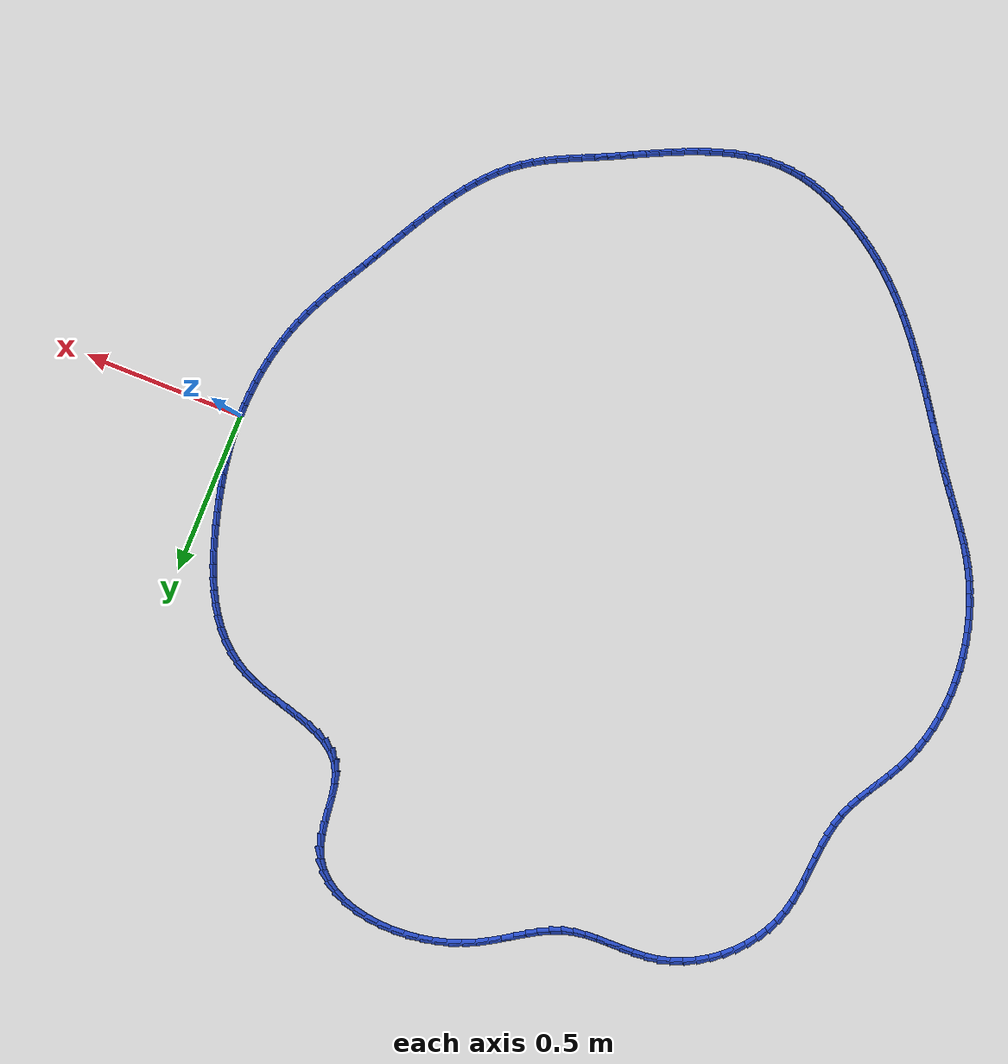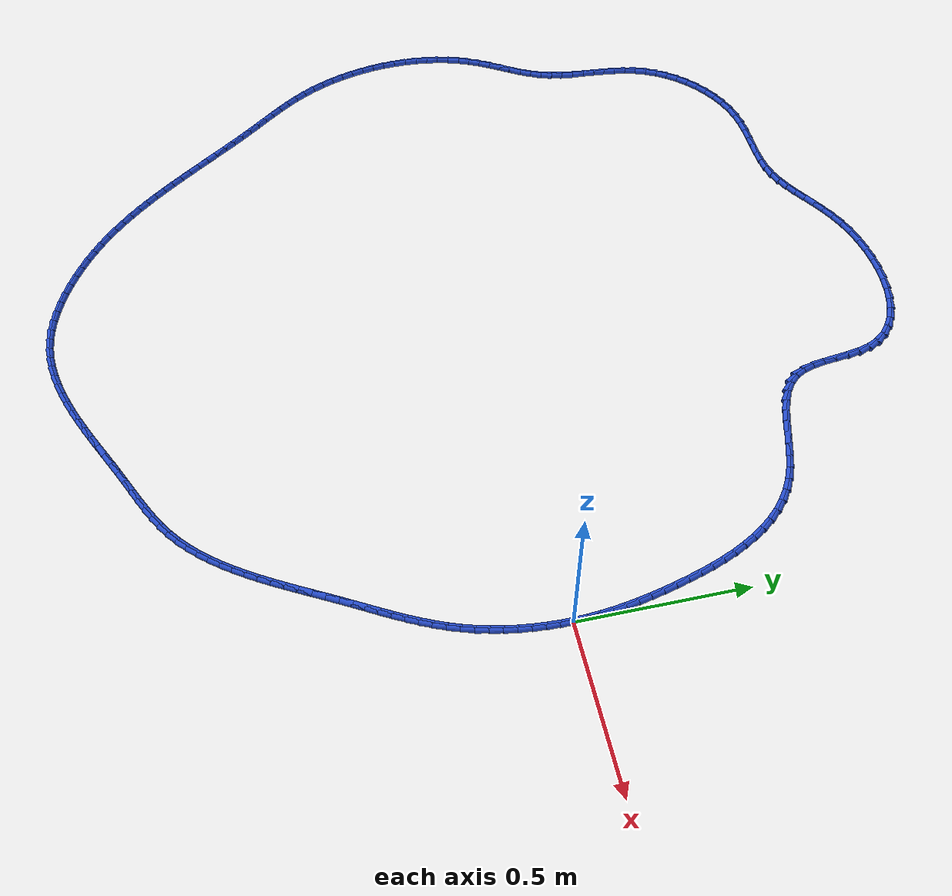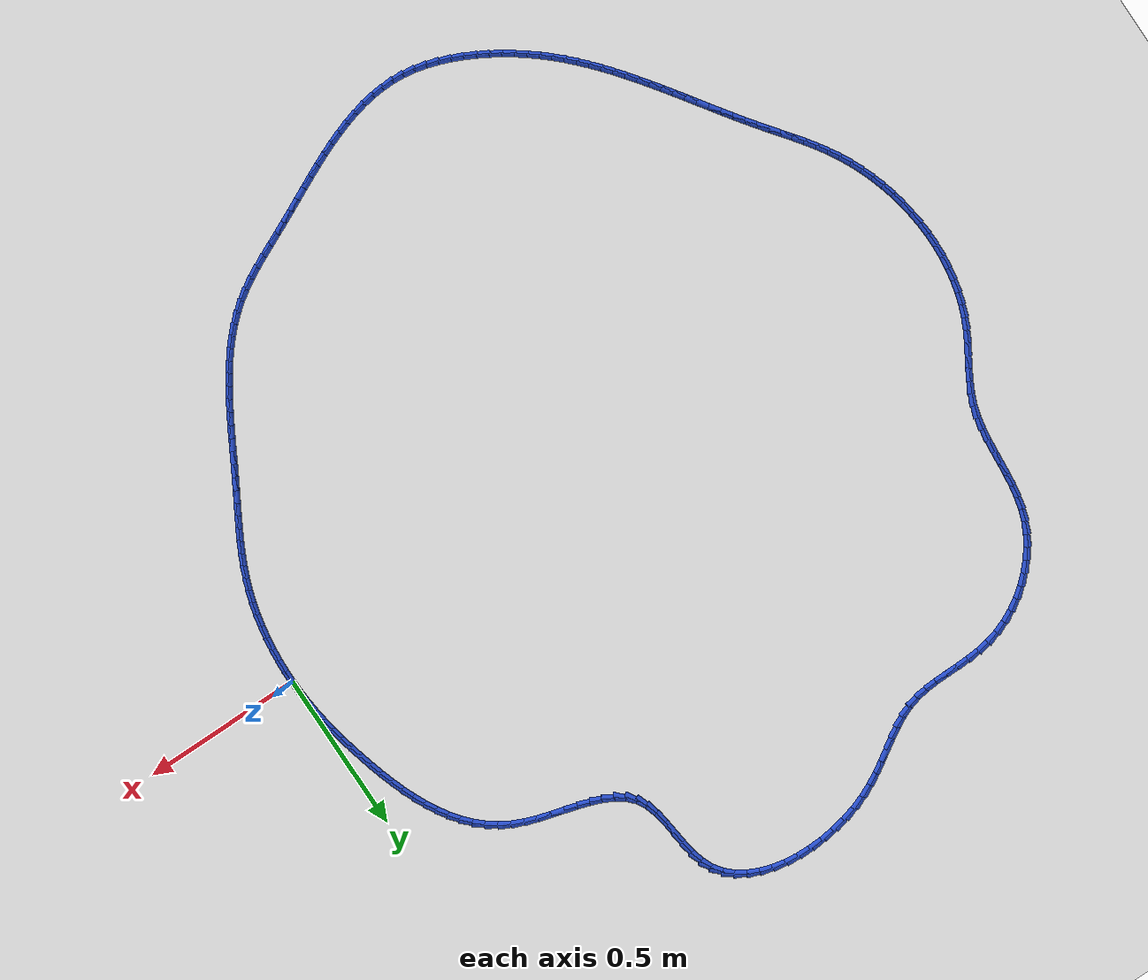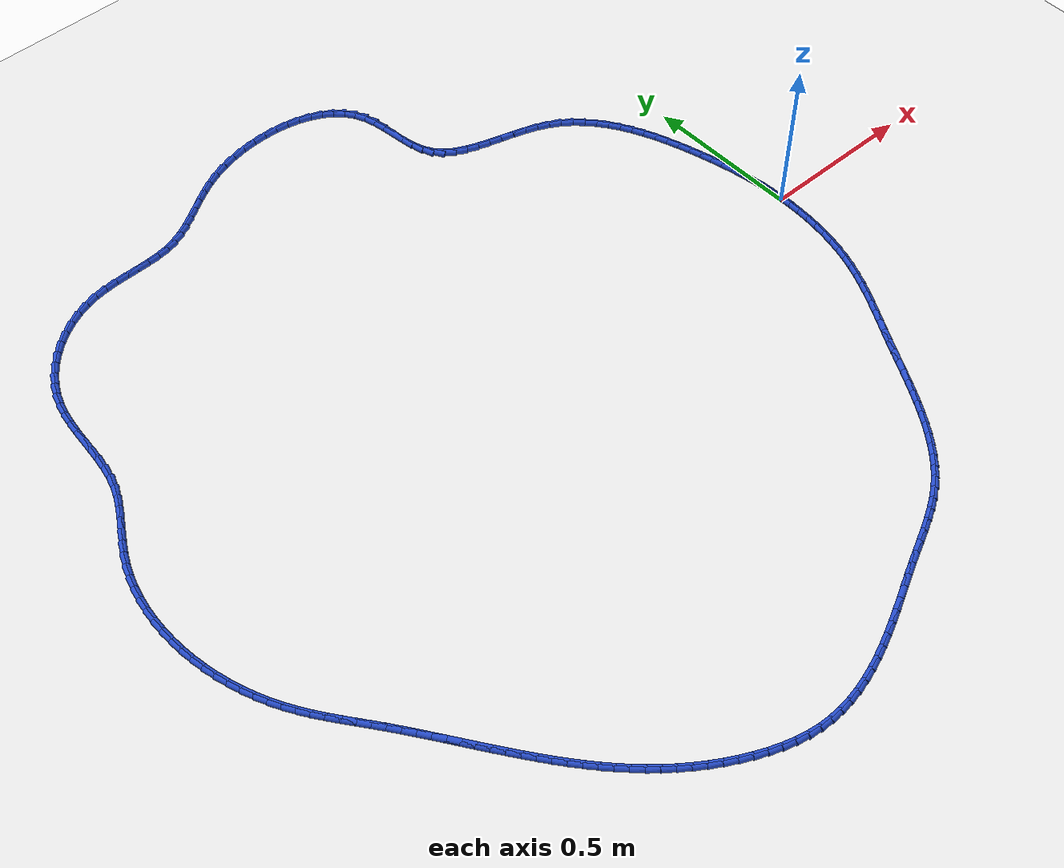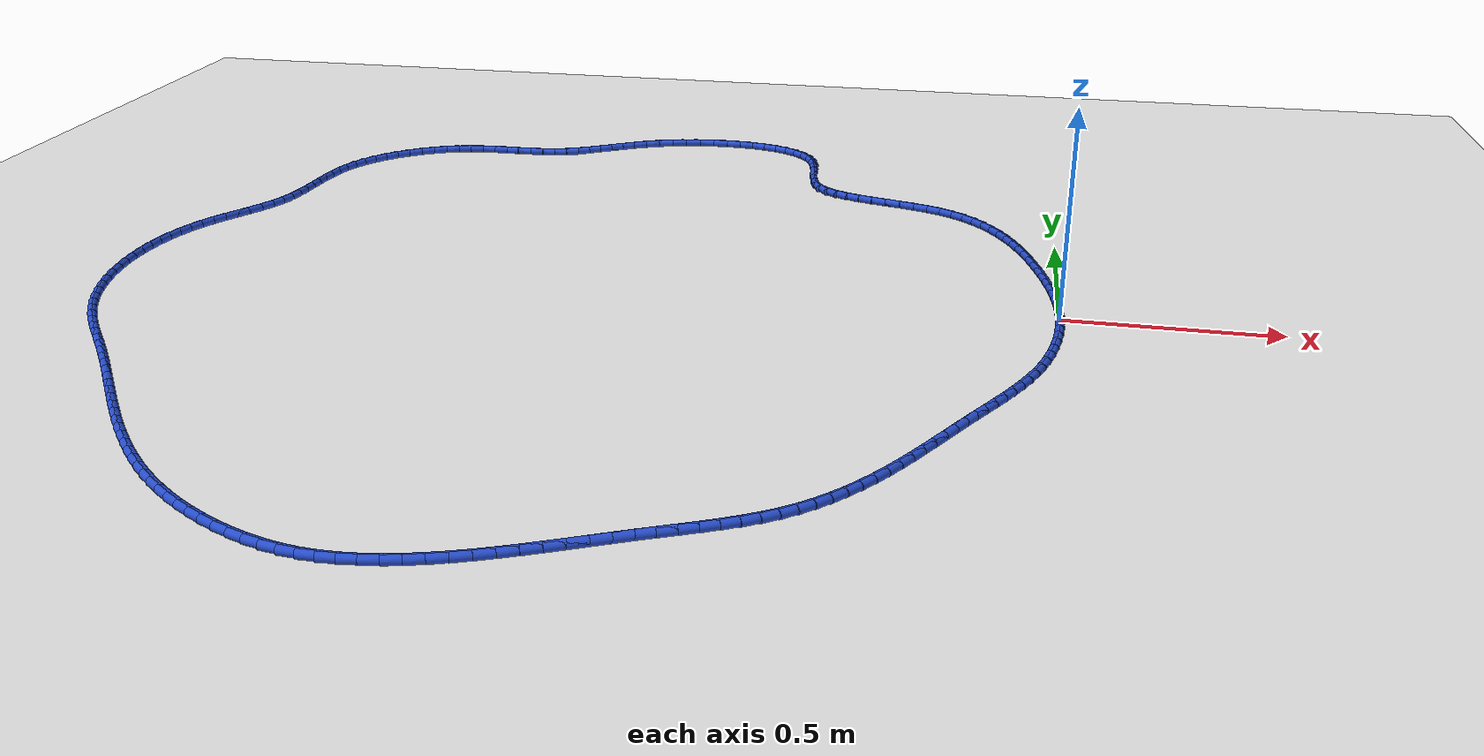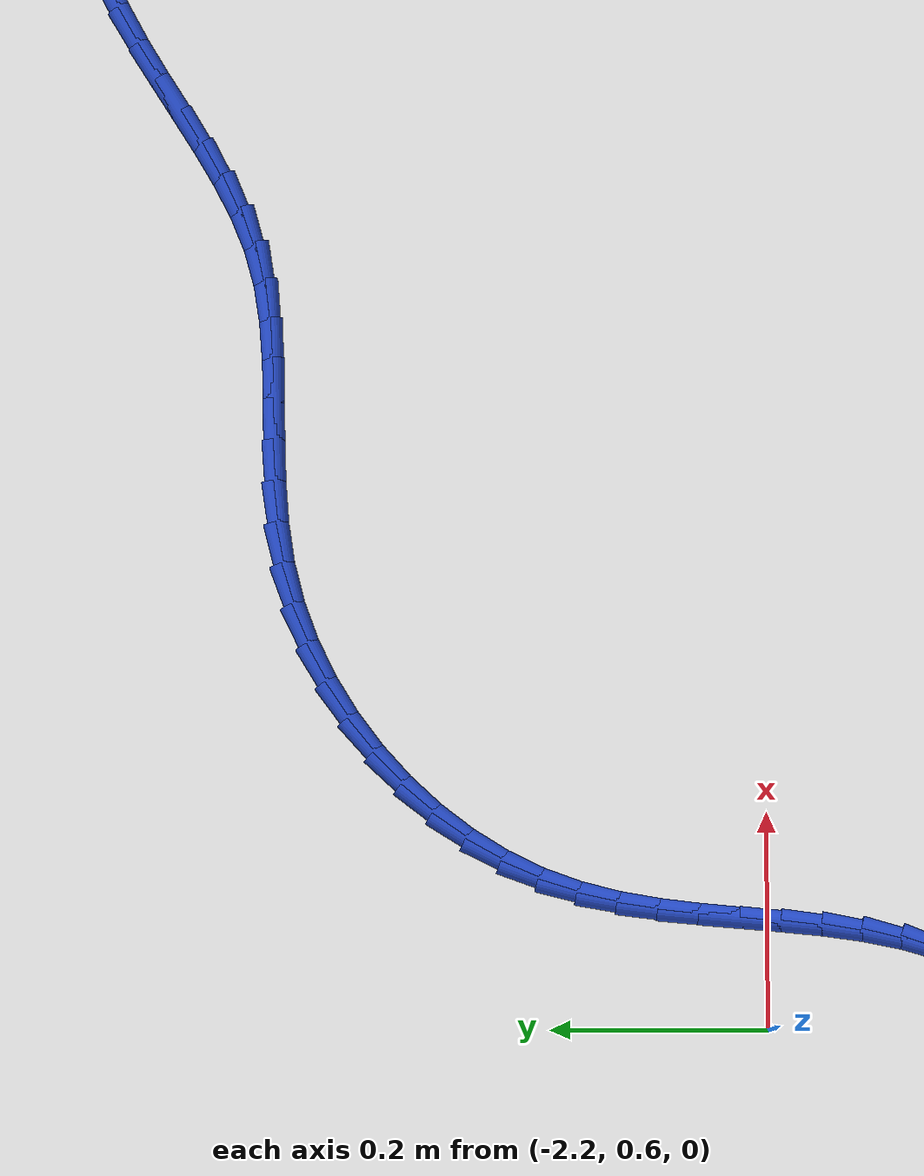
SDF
<sdf version="1.6">
 <world name="default">
  <light name="sun" type="directional">
   <pose>0 0 10 0 -0 0</pose>
   <diffuse>0.8 0.8 0.8 1</diffuse>
   <specular>0.2 0.2 0.2 1</specular>
   <attenuation>
    <range>1000</range>
    <constant>0.9</constant>
    <linear>0.01</linear>
    <quadratic>0.001</quadratic>
   </attenuation>
   <direction>-0.5 0.1 -0.9</direction>
  </light>
  <model name="ground_plane">
   <static>1</static>
   <link name="link">
    <collision name="collision">
     <geometry><plane><normal>0 0 1</normal><size>100 100</size></plane></geometry>
     <surface><friction><ode><mu>100</mu><mu2>50</mu2></ode></friction></surface>
    </collision>
    <visual name="visual">
     <cast_shadows>0</cast_shadows>
     <geometry><plane><normal>0 0 1</normal><size>100 100</size></plane></geometry>
     <material>
      <script><uri>file://media/materials/scripts/gazebo.material</uri><name>Gazebo/WhiteGlow</name></script>
     </material>
    </visual>
   </link>
  </model>
  <gravity>0 0 -9.8</gravity>
  <magnetic_field>6e-06 2.3e-05 -4.2e-05</magnetic_field>
  <atmosphere type="adiabatic"/>
  <physics name="default_physics" default="0" type="ode">
   <max_step_size>0.001</max_step_size>
   <real_time_factor>1</real_time_factor>
   <real_time_update_rate>1000</real_time_update_rate>
  </physics>
  <scene><ambient>0.4 0.4 0.4 1</ambient><background>0.7 0.7 0.7 1</background><shadows>1</shadows></scene>
  <spherical_coordinates>
   <surface_model>EARTH_WGS84</surface_model>
   <latitude_deg>0</latitude_deg>
   <longitude_deg>0</longitude_deg>
   <elevation>0</elevation>
   <heading_deg>0</heading_deg>
  </spherical_coordinates>
  <model name="line">
   <link name="link_0">
    <pose>2.0816681711721685e-17 -3.469446951953614e-17 0.01 0 1.57 -1.535175717402976</pose>
    <collision name="collision">
     <geometry><cylinder><radius>0.01</radius><length>0.08</length></cylinder></geometry>
    </collision>
    <visual name="visual">
     <material>
      <script><name>Gazebo/Blue</name><uri>file://media/materials/scripts/gazebo.material</uri></script>
     </material>
     <geometry><cylinder><radius>0.01</radius><length>0.08</length></cylinder></geometry>
    </visual>
   </link>
   <link name="link_1">
    <pose>-0.0013238660518585024 0.03715001252713658 0.01 0 1.57 -1.4973385119002325</pose>
    <collision name="collision">
     <geometry><cylinder><radius>0.01</radius><length>0.08</length></cylinder></geometry>
    </collision>
    <visual name="visual">
     <material>
      <script><name>Gazebo/Blue</name><uri>file://media/materials/scripts/gazebo.material</uri></script>
     </material>
     <geometry><cylinder><radius>0.01</radius><length>0.08</length></cylinder></geometry>
    </visual>
   </link>
   <link name="link_2">
    <pose>-0.004042059239383102 0.07408688932368357 0.01 0 1.57 -1.4615958930958368</pose>
    <collision name="collision">
     <geometry><cylinder><radius>0.01</radius><length>0.08</length></cylinder></geometry>
    </collision>
    <visual name="visual">
     <material>
      <script><name>Gazebo/Blue</name><uri>file://media/materials/scripts/gazebo.material</uri></script>
     </material>
     <geometry><cylinder><radius>0.01</radius><length>0.08</length></cylinder></geometry>
    </visual>
   </link>
   <link name="link_3">
    <pose>-0.008076136931947968 0.11088188813671723 0.01 0 1.57 -1.4282274077855395</pose>
    <collision name="collision">
     <geometry><cylinder><radius>0.01</radius><length>0.08</length></cylinder></geometry>
    </collision>
    <visual name="visual">
     <material>
      <script><name>Gazebo/Blue</name><uri>file://media/materials/scripts/gazebo.material</uri></script>
     </material>
     <geometry><cylinder><radius>0.01</radius><length>0.08</length></cylinder></geometry>
    </visual>
   </link>
   <link name="link_4">
    <pose>-0.01334765649892731 0.14760626671331398 0.01 0 1.57 -1.397454465860084</pose>
    <collision name="collision">
     <geometry><cylinder><radius>0.01</radius><length>0.08</length></cylinder></geometry>
    </collision>
    <visual name="visual">
     <material>
      <script><name>Gazebo/Blue</name><uri>file://media/materials/scripts/gazebo.material</uri></script>
     </material>
     <geometry><cylinder><radius>0.01</radius><length>0.08</length></cylinder></geometry>
    </visual>
   </link>
   <link name="link_5">
    <pose>-0.01977817530969532 0.18433128280055017 0.01 0 1.57 -1.3694400405301053</pose>
    <collision name="collision">
     <geometry><cylinder><radius>0.01</radius><length>0.08</length></cylinder></geometry>
    </collision>
    <visual name="visual">
     <material>
      <script><name>Gazebo/Blue</name><uri>file://media/materials/scripts/gazebo.material</uri></script>
     </material>
     <geometry><cylinder><radius>0.01</radius><length>0.08</length></cylinder></geometry>
    </visual>
   </link>
   <link name="link_6">
    <pose>-0.027289250733626223 0.22112819414550225 0.01 0 1.57 -1.344291552297304</pose>
    <collision name="collision">
     <geometry><cylinder><radius>0.01</radius><length>0.08</length></cylinder></geometry>
    </collision>
    <visual name="visual">
     <material>
      <script><name>Gazebo/Blue</name><uri>file://media/materials/scripts/gazebo.material</uri></script>
     </material>
     <geometry><cylinder><radius>0.01</radius><length>0.08</length></cylinder></geometry>
    </visual>
   </link>
   <link name="link_7">
    <pose>-0.0358024401400942 0.25806825849524656 0.01 0 1.57 -1.3220660199620342</pose>
    <collision name="collision">
     <geometry><cylinder><radius>0.01</radius><length>0.08</length></cylinder></geometry>
    </collision>
    <visual name="visual">
     <material>
      <script><name>Gazebo/Blue</name><uri>file://media/materials/scripts/gazebo.material</uri></script>
     </material>
     <geometry><cylinder><radius>0.01</radius><length>0.08</length></cylinder></geometry>
    </visual>
   </link>
   <link name="link_8">
    <pose>-0.04523930089847343 0.2952227335968594 0.01 0 1.57 -1.3024077015015403</pose>
    <collision name="collision">
     <geometry><cylinder><radius>0.01</radius><length>0.08</length></cylinder></geometry>
    </collision>
    <visual name="visual">
     <material>
      <script><name>Gazebo/Blue</name><uri>file://media/materials/scripts/gazebo.material</uri></script>
     </material>
     <geometry><cylinder><radius>0.01</radius><length>0.08</length></cylinder></geometry>
    </visual>
   </link>
   <link name="link_9">
    <pose>-0.055532059470506975 0.33264766549137953 0.01 0 1.57 -1.2803683684279992</pose>
    <collision name="collision">
     <geometry><cylinder><radius>0.01</radius><length>0.08</length></cylinder></geometry>
    </collision>
    <visual name="visual">
     <material>
      <script><name>Gazebo/Blue</name><uri>file://media/materials/scripts/gazebo.material</uri></script>
     </material>
     <geometry><cylinder><radius>0.01</radius><length>0.08</length></cylinder></geometry>
    </visual>
   </link>
   <link name="link_10">
    <pose>-0.06675474178443426 0.3701969263398103 0.01 0 1.57 -1.252274470634638</pose>
    <collision name="collision">
     <geometry><cylinder><radius>0.01</radius><length>0.08</length></cylinder></geometry>
    </collision>
    <visual name="visual">
     <material>
      <script><name>Gazebo/Blue</name><uri>file://media/materials/scripts/gazebo.material</uri></script>
     </material>
     <geometry><cylinder><radius>0.01</radius><length>0.08</length></cylinder></geometry>
    </visual>
   </link>
   <link name="link_11">
    <pose>-0.07908207017894514 0.4075808180591378 0.01 0 1.57 -1.217695955242727</pose>
    <collision name="collision">
     <geometry><cylinder><radius>0.01</radius><length>0.08</length></cylinder></geometry>
    </collision>
    <visual name="visual">
     <material>
      <script><name>Gazebo/Blue</name><uri>file://media/materials/scripts/gazebo.material</uri></script>
     </material>
     <geometry><cylinder><radius>0.01</radius><length>0.08</length></cylinder></geometry>
    </visual>
   </link>
   <link name="link_12">
    <pose>-0.09269091233070037 0.4445065838009506 0.01 0 1.57 -1.1761381614254764</pose>
    <collision name="collision">
     <geometry><cylinder><radius>0.01</radius><length>0.08</length></cylinder></geometry>
    </collision>
    <visual name="visual">
     <material>
      <script><name>Gazebo/Blue</name><uri>file://media/materials/scripts/gazebo.material</uri></script>
     </material>
     <geometry><cylinder><radius>0.01</radius><length>0.08</length></cylinder></geometry>
    </visual>
   </link>
   <link name="link_13">
    <pose>-0.10775813591636066 0.48068146671683687 0.01 0 1.57 -1.1269966102576379</pose>
    <collision name="collision">
     <geometry><cylinder><radius>0.01</radius><length>0.08</length></cylinder></geometry>
    </collision>
    <visual name="visual">
     <material>
      <script><name>Gazebo/Blue</name><uri>file://media/materials/scripts/gazebo.material</uri></script>
     </material>
     <geometry><cylinder><radius>0.01</radius><length>0.08</length></cylinder></geometry>
    </visual>
   </link>
   <link name="link_14">
    <pose>-0.12446060861258675 0.5158127099583852 0.01 0 1.57 -1.0696034037154103</pose>
    <collision name="collision">
     <geometry><cylinder><radius>0.01</radius><length>0.08</length></cylinder></geometry>
    </collision>
    <visual name="visual">
     <material>
      <script><name>Gazebo/Blue</name><uri>file://media/materials/scripts/gazebo.material</uri></script>
     </material>
     <geometry><cylinder><radius>0.01</radius><length>0.08</length></cylinder></geometry>
    </visual>
   </link>
   <link name="link_15">
    <pose>-0.14297519809603929 0.5496075566771841 0.01 0 1.57 -1.0033041421238134</pose>
    <collision name="collision">
     <geometry><cylinder><radius>0.01</radius><length>0.08</length></cylinder></geometry>
    </collision>
    <visual name="visual">
     <material>
      <script><name>Gazebo/Blue</name><uri>file://media/materials/scripts/gazebo.material</uri></script>
     </material>
     <geometry><cylinder><radius>0.01</radius><length>0.08</length></cylinder></geometry>
    </visual>
   </link>
   <link name="link_16">
    <pose>-0.1634787720433791 0.5817732500248217 0.01 0 1.57 -0.9275790790610703</pose>
    <collision name="collision">
     <geometry><cylinder><radius>0.01</radius><length>0.08</length></cylinder></geometry>
    </collision>
    <visual name="visual">
     <material>
      <script><name>Gazebo/Blue</name><uri>file://media/materials/scripts/gazebo.material</uri></script>
     </material>
     <geometry><cylinder><radius>0.01</radius><length>0.08</length></cylinder></geometry>
    </visual>
   </link>
   <link name="link_17">
    <pose>-0.18614819813126682 0.6120170331528866 0.01 0 1.57 -0.8422166240656386</pose>
    <collision name="collision">
     <geometry><cylinder><radius>0.01</radius><length>0.08</length></cylinder></geometry>
    </collision>
    <visual name="visual">
     <material>
      <script><name>Gazebo/Blue</name><uri>file://media/materials/scripts/gazebo.material</uri></script>
     </material>
     <geometry><cylinder><radius>0.01</radius><length>0.08</length></cylinder></geometry>
    </visual>
   </link>
   <link name="link_18">
    <pose>-0.2111603440363632 0.6400461492129671 0.01 0 1.57 -0.7475291605570913</pose>
    <collision name="collision">
     <geometry><cylinder><radius>0.01</radius><length>0.08</length></cylinder></geometry>
    </collision>
    <visual name="visual">
     <material>
      <script><name>Gazebo/Blue</name><uri>file://media/materials/scripts/gazebo.material</uri></script>
     </material>
     <geometry><cylinder><radius>0.01</radius><length>0.08</length></cylinder></geometry>
    </visual>
   </link>
   <link name="link_19">
    <pose>-0.23869207743532894 0.6655678413566518 0.01 0 1.57 -0.644566703357554</pose>
    <collision name="collision">
     <geometry><cylinder><radius>0.01</radius><length>0.08</length></cylinder></geometry>
    </collision>
    <visual name="visual">
     <material>
      <script><name>Gazebo/Blue</name><uri>file://media/materials/scripts/gazebo.material</uri></script>
     </material>
     <geometry><cylinder><radius>0.01</radius><length>0.08</length></cylinder></geometry>
    </visual>
   </link>
   <link name="link_20">
    <pose>-0.26892026600482477 0.6882893527355289 0.01 0 1.57 -0.5352426293206431</pose>
    <collision name="collision">
     <geometry><cylinder><radius>0.01</radius><length>0.08</length></cylinder></geometry>
    </collision>
    <visual name="visual">
     <material>
      <script><name>Gazebo/Blue</name><uri>file://media/materials/scripts/gazebo.material</uri></script>
     </material>
     <geometry><cylinder><radius>0.01</radius><length>0.08</length></cylinder></geometry>
    </visual>
   </link>
   <link name="link_21">
    <pose>-0.3020217774215115 0.707917926501187 0.01 0 1.57 -0.4273907402431438</pose>
    <collision name="collision">
     <geometry><cylinder><radius>0.01</radius><length>0.08</length></cylinder></geometry>
    </collision>
    <visual name="visual">
     <material>
      <script><name>Gazebo/Blue</name><uri>file://media/materials/scripts/gazebo.material</uri></script>
     </material>
     <geometry><cylinder><radius>0.01</radius><length>0.08</length></cylinder></geometry>
    </visual>
   </link>
   <link name="link_22">
    <pose>-0.33802448139929814 0.7243159598901089 0.01 0 1.57 -0.3464352621083043</pose>
    <collision name="collision">
     <geometry><cylinder><radius>0.01</radius><length>0.08</length></cylinder></geometry>
    </collision>
    <visual name="visual">
     <material>
      <script><name>Gazebo/Blue</name><uri>file://media/materials/scripts/gazebo.material</uri></script>
     </material>
     <geometry><cylinder><radius>0.01</radius><length>0.08</length></cylinder></geometry>
    </visual>
   </link>
   <link name="link_23">
    <pose>-0.37622585044728296 0.7381064250340952 0.01 0 1.57 -0.2960136077869675</pose>
    <collision name="collision">
     <geometry><cylinder><radius>0.01</radius><length>0.08</length></cylinder></geometry>
    </collision>
    <visual name="visual">
     <material>
      <script><name>Gazebo/Blue</name><uri>file://media/materials/scripts/gazebo.material</uri></script>
     </material>
     <geometry><cylinder><radius>0.01</radius><length>0.08</length></cylinder></geometry>
    </visual>
   </link>
   <link name="link_24">
    <pose>-0.4156999069195276 0.7501449764700213 0.01 0 1.57 -0.2728352720622941</pose>
    <collision name="collision">
     <geometry><cylinder><radius>0.01</radius><length>0.08</length></cylinder></geometry>
    </collision>
    <visual name="visual">
     <material>
      <script><name>Gazebo/Blue</name><uri>file://media/materials/scripts/gazebo.material</uri></script>
     </material>
     <geometry><cylinder><radius>0.01</radius><length>0.08</length></cylinder></geometry>
    </visual>
   </link>
   <link name="link_25">
    <pose>-0.455520616364132 0.7612873278877661 0.01 0 1.57 -0.275707484339287</pose>
    <collision name="collision">
     <geometry><cylinder><radius>0.01</radius><length>0.08</length></cylinder></geometry>
    </collision>
    <visual name="visual">
     <material>
      <script><name>Gazebo/Blue</name><uri>file://media/materials/scripts/gazebo.material</uri></script>
     </material>
     <geometry><cylinder><radius>0.01</radius><length>0.08</length></cylinder></geometry>
    </visual>
   </link>
   <link name="link_26">
    <pose>-0.49476194432919585 0.7723891929772085 0.01 0 1.57 -0.3058906463517367</pose>
    <collision name="collision">
     <geometry><cylinder><radius>0.01</radius><length>0.08</length></cylinder></geometry>
    </collision>
    <visual name="visual">
     <material>
      <script><name>Gazebo/Blue</name><uri>file://media/materials/scripts/gazebo.material</uri></script>
     </material>
     <geometry><cylinder><radius>0.01</radius><length>0.08</length></cylinder></geometry>
    </visual>
   </link>
   <link name="link_27">
    <pose>-0.5324978563628189 0.7843062854282274 0.01 0 1.57 -0.3674056191721325</pose>
    <collision name="collision">
     <geometry><cylinder><radius>0.01</radius><length>0.08</length></cylinder></geometry>
    </collision>
    <visual name="visual">
     <material>
      <script><name>Gazebo/Blue</name><uri>file://media/materials/scripts/gazebo.material</uri></script>
     </material>
     <geometry><cylinder><radius>0.01</radius><length>0.08</length></cylinder></geometry>
    </visual>
   </link>
   <link name="link_28">
    <pose>-0.5678023180131009 0.7978943189307018 0.01 0 1.57 -0.46717720896954856</pose>
    <collision name="collision">
     <geometry><cylinder><radius>0.01</radius><length>0.08</length></cylinder></geometry>
    </collision>
    <visual name="visual">
     <material>
      <script><name>Gazebo/Blue</name><uri>file://media/materials/scripts/gazebo.material</uri></script>
     </material>
     <geometry><cylinder><radius>0.01</radius><length>0.08</length></cylinder></geometry>
    </visual>
   </link>
   <link name="link_29">
    <pose>-0.5997492948281414 0.8140090071745106 0.01 0 1.57 -0.6139366025843185</pose>
    <collision name="collision">
     <geometry><cylinder><radius>0.01</radius><length>0.08</length></cylinder></geometry>
    </collision>
    <visual name="visual">
     <material>
      <script><name>Gazebo/Blue</name><uri>file://media/materials/scripts/gazebo.material</uri></script>
     </material>
     <geometry><cylinder><radius>0.01</radius><length>0.08</length></cylinder></geometry>
    </visual>
   </link>
   <link name="link_30">
    <pose>-0.627412752356041 0.8335060638495331 0.01 0 1.57 -0.8131299905219594</pose>
    <collision name="collision">
     <geometry><cylinder><radius>0.01</radius><length>0.08</length></cylinder></geometry>
    </collision>
    <visual name="visual">
     <material>
      <script><name>Gazebo/Blue</name><uri>file://media/materials/scripts/gazebo.material</uri></script>
     </material>
     <geometry><cylinder><radius>0.01</radius><length>0.08</length></cylinder></geometry>
    </visual>
   </link>
   <link name="link_31">
    <pose>-0.6498666561448985 0.8572412026456475 0.01 0 1.57 -1.0531341289875311</pose>
    <collision name="collision">
     <geometry><cylinder><radius>0.01</radius><length>0.08</length></cylinder></geometry>
    </collision>
    <visual name="visual">
     <material>
      <script><name>Gazebo/Blue</name><uri>file://media/materials/scripts/gazebo.material</uri></script>
     </material>
     <geometry><cylinder><radius>0.01</radius><length>0.08</length></cylinder></geometry>
    </visual>
   </link>
   <link name="link_32">
    <pose>-0.6662520378113883 0.8860146556217079 0.01 0 1.57 -1.2587014514623511</pose>
    <collision name="collision">
     <geometry><cylinder><radius>0.01</radius><length>0.08</length></cylinder></geometry>
    </collision>
    <visual name="visual">
     <material>
      <script><name>Gazebo/Blue</name><uri>file://media/materials/scripts/gazebo.material</uri></script>
     </material>
     <geometry><cylinder><radius>0.01</radius><length>0.08</length></cylinder></geometry>
    </visual>
   </link>
   <link name="link_33">
    <pose>-0.6770591071181126 0.9195105225557909 0.01 0 1.57 -1.383983918766557</pose>
    <collision name="collision">
     <geometry><cylinder><radius>0.01</radius><length>0.08</length></cylinder></geometry>
    </collision>
    <visual name="visual">
     <material>
      <script><name>Gazebo/Blue</name><uri>file://media/materials/scripts/gazebo.material</uri></script>
     </material>
     <geometry><cylinder><radius>0.01</radius><length>0.08</length></cylinder></geometry>
    </visual>
   </link>
   <link name="link_34">
    <pose>-0.6840278526906737 0.9563790008187679 0.01 0 1.57 -1.4448951045219727</pose>
    <collision name="collision">
     <geometry><cylinder><radius>0.01</radius><length>0.08</length></cylinder></geometry>
    </collision>
    <visual name="visual">
     <material>
      <script><name>Gazebo/Blue</name><uri>file://media/materials/scripts/gazebo.material</uri></script>
     </material>
     <geometry><cylinder><radius>0.01</radius><length>0.08</length></cylinder></geometry>
    </visual>
   </link>
   <link name="link_35">
    <pose>-0.6889454128609842 0.9952312823251865 0.01 0 1.57 -1.4533711151475703</pose>
    <collision name="collision">
     <geometry><cylinder><radius>0.01</radius><length>0.08</length></cylinder></geometry>
    </collision>
    <visual name="visual">
     <material>
      <script><name>Gazebo/Blue</name><uri>file://media/materials/scripts/gazebo.material</uri></script>
     </material>
     <geometry><cylinder><radius>0.01</radius><length>0.08</length></cylinder></geometry>
    </visual>
   </link>
   <link name="link_36">
    <pose>-0.6935989259609571 1.0346785589895953 0.01 0 1.57 -1.4123416067688785</pose>
    <collision name="collision">
     <geometry><cylinder><radius>0.01</radius><length>0.08</length></cylinder></geometry>
    </collision>
    <visual name="visual">
     <material>
      <script><name>Gazebo/Blue</name><uri>file://media/materials/scripts/gazebo.material</uri></script>
     </material>
     <geometry><cylinder><radius>0.01</radius><length>0.08</length></cylinder></geometry>
    </visual>
   </link>
   <link name="link_37">
    <pose>-0.6997755303225047 1.0733320227265424 0.01 0 1.57 -1.3163148851048265</pose>
    <collision name="collision">
     <geometry><cylinder><radius>0.01</radius><length>0.08</length></cylinder></geometry>
    </collision>
    <visual name="visual">
     <material>
      <script><name>Gazebo/Blue</name><uri>file://media/materials/scripts/gazebo.material</uri></script>
     </material>
     <geometry><cylinder><radius>0.01</radius><length>0.08</length></cylinder></geometry>
    </visual>
   </link>
   <link name="link_38">
    <pose>-0.7092623642775403 1.109802865450576 0.01 0 1.57 -1.1543245672321736</pose>
    <collision name="collision">
     <geometry><cylinder><radius>0.01</radius><length>0.08</length></cylinder></geometry>
    </collision>
    <visual name="visual">
     <material>
      <script><name>Gazebo/Blue</name><uri>file://media/materials/scripts/gazebo.material</uri></script>
     </material>
     <geometry><cylinder><radius>0.01</radius><length>0.08</length></cylinder></geometry>
    </visual>
   </link>
   <link name="link_39">
    <pose>-0.7238220319621379 1.1427174261493862 0.01 0 1.57 -0.9514174282157696</pose>
    <collision name="collision">
     <geometry><cylinder><radius>0.01</radius><length>0.08</length></cylinder></geometry>
    </collision>
    <visual name="visual">
     <material>
      <script><name>Gazebo/Blue</name><uri>file://media/materials/scripts/gazebo.material</uri></script>
     </material>
     <geometry><cylinder><radius>0.01</radius><length>0.08</length></cylinder></geometry>
    </visual>
   </link>
   <link name="link_40">
    <pose>-0.7442152736061436 1.171320580728098 0.01 0 1.57 -0.7594153593585119</pose>
    <collision name="collision">
     <geometry><cylinder><radius>0.01</radius><length>0.08</length></cylinder></geometry>
    </collision>
    <visual name="visual">
     <material>
      <script><name>Gazebo/Blue</name><uri>file://media/materials/scripts/gazebo.material</uri></script>
     </material>
     <geometry><cylinder><radius>0.01</radius><length>0.08</length></cylinder></geometry>
    </visual>
   </link>
   <link name="link_41">
    <pose>-0.7698728434317024 1.1956783200559753 0.01 0 1.57 -0.589399324187846</pose>
    <collision name="collision">
     <geometry><cylinder><radius>0.01</radius><length>0.08</length></cylinder></geometry>
    </collision>
    <visual name="visual">
     <material>
      <script><name>Gazebo/Blue</name><uri>file://media/materials/scripts/gazebo.material</uri></script>
     </material>
     <geometry><cylinder><radius>0.01</radius><length>0.08</length></cylinder></geometry>
    </visual>
   </link>
   <link name="link_42">
    <pose>-0.8001336814655065 1.2159133198165366 0.01 0 1.57 -0.4431737044444387</pose>
    <collision name="collision">
     <geometry><cylinder><radius>0.01</radius><length>0.08</length></cylinder></geometry>
    </collision>
    <visual name="visual">
     <material>
      <script><name>Gazebo/Blue</name><uri>file://media/materials/scripts/gazebo.material</uri></script>
     </material>
     <geometry><cylinder><radius>0.01</radius><length>0.08</length></cylinder></geometry>
    </visual>
   </link>
   <link name="link_43">
    <pose>-0.8343367277342487 1.2321482556933 0.01 0 1.57 -0.31845314572352396</pose>
    <collision name="collision">
     <geometry><cylinder><radius>0.01</radius><length>0.08</length></cylinder></geometry>
    </collision>
    <visual name="visual">
     <material>
      <script><name>Gazebo/Blue</name><uri>file://media/materials/scripts/gazebo.material</uri></script>
     </material>
     <geometry><cylinder><radius>0.01</radius><length>0.08</length></cylinder></geometry>
    </visual>
   </link>
   <link name="link_44">
    <pose>-0.8718209222646209 1.2445058033697833 0.01 0 1.57 -0.21130932264771743</pose>
    <collision name="collision">
     <geometry><cylinder><radius>0.01</radius><length>0.08</length></cylinder></geometry>
    </collision>
    <visual name="visual">
     <material>
      <script><name>Gazebo/Blue</name><uri>file://media/materials/scripts/gazebo.material</uri></script>
     </material>
     <geometry><cylinder><radius>0.01</radius><length>0.08</length></cylinder></geometry>
    </visual>
   </link>
   <link name="link_45">
    <pose>-0.9119252050833155 1.253108638529505 0.01 0 1.57 -0.11762866173863026</pose>
    <collision name="collision">
     <geometry><cylinder><radius>0.01</radius><length>0.08</length></cylinder></geometry>
    </collision>
    <visual name="visual">
     <material>
      <script><name>Gazebo/Blue</name><uri>file://media/materials/scripts/gazebo.material</uri></script>
     </material>
     <geometry><cylinder><radius>0.01</radius><length>0.08</length></cylinder></geometry>
    </visual>
   </link>
   <link name="link_46">
    <pose>-0.9539885162170249 1.2580794368559822 0.01 0 1.57 -0.03369098426128056</pose>
    <collision name="collision">
     <geometry><cylinder><radius>0.01</radius><length>0.08</length></cylinder></geometry>
    </collision>
    <visual name="visual">
     <material>
      <script><name>Gazebo/Blue</name><uri>file://media/materials/scripts/gazebo.material</uri></script>
     </material>
     <geometry><cylinder><radius>0.01</radius><length>0.08</length></cylinder></geometry>
    </visual>
   </link>
   <link name="link_47">
    <pose>-0.9973497956924415 1.2595408740327343 0.01 0 1.57 0.043729549484648085</pose>
    <collision name="collision">
     <geometry><cylinder><radius>0.01</radius><length>0.08</length></cylinder></geometry>
    </collision>
    <visual name="visual">
     <material>
      <script><name>Gazebo/Blue</name><uri>file://media/materials/scripts/gazebo.material</uri></script>
     </material>
     <geometry><cylinder><radius>0.01</radius><length>0.08</length></cylinder></geometry>
    </visual>
   </link>
   <link name="link_48">
    <pose>-1.0413479835362567 1.2576156257432782 0.01 0 1.57 0.1174640705244743</pose>
    <collision name="collision">
     <geometry><cylinder><radius>0.01</radius><length>0.08</length></cylinder></geometry>
    </collision>
    <visual name="visual">
     <material>
      <script><name>Gazebo/Blue</name><uri>file://media/materials/scripts/gazebo.material</uri></script>
     </material>
     <geometry><cylinder><radius>0.01</radius><length>0.08</length></cylinder></geometry>
    </visual>
   </link>
   <link name="link_49">
    <pose>-1.0853220197751645 1.2524263676711336 0.01 0 1.57 0.1901178955462986</pose>
    <collision name="collision">
     <geometry><cylinder><radius>0.01</radius><length>0.08</length></cylinder></geometry>
    </collision>
    <visual name="visual">
     <material>
      <script><name>Gazebo/Blue</name><uri>file://media/materials/scripts/gazebo.material</uri></script>
     </material>
     <geometry><cylinder><radius>0.01</radius><length>0.08</length></cylinder></geometry>
    </visual>
   </link>
   <link name="link_50">
    <pose>-1.1286108444358562 1.2440957754998168 0.01 0 1.57 0.26426200059418714</pose>
    <collision name="collision">
     <geometry><cylinder><radius>0.01</radius><length>0.08</length></cylinder></geometry>
    </collision>
    <visual name="visual">
     <material>
      <script><name>Gazebo/Blue</name><uri>file://media/materials/scripts/gazebo.material</uri></script>
     </material>
     <geometry><cylinder><radius>0.01</radius><length>0.08</length></cylinder></geometry>
    </visual>
   </link>
   <link name="link_51">
    <pose>-1.170553397545024 1.2327465249128464 0.01 0 1.57 0.3426386730582417</pose>
    <collision name="collision">
     <geometry><cylinder><radius>0.01</radius><length>0.08</length></cylinder></geometry>
    </collision>
    <visual name="visual">
     <material>
      <script><name>Gazebo/Blue</name><uri>file://media/materials/scripts/gazebo.material</uri></script>
     </material>
     <geometry><cylinder><radius>0.01</radius><length>0.08</length></cylinder></geometry>
    </visual>
   </link>
   <link name="link_52">
    <pose>-1.2104886191293602 1.218501291593741 0.01 0 1.57 0.4252972591554823</pose>
    <collision name="collision">
     <geometry><cylinder><radius>0.01</radius><length>0.08</length></cylinder></geometry>
    </collision>
    <visual name="visual">
     <material>
      <script><name>Gazebo/Blue</name><uri>file://media/materials/scripts/gazebo.material</uri></script>
     </material>
     <geometry><cylinder><radius>0.01</radius><length>0.08</length></cylinder></geometry>
    </visual>
   </link>
   <link name="link_53">
    <pose>-1.2478857526575253 1.201562583528729 0.01 0 1.57 0.49515200709090307</pose>
    <collision name="collision">
     <geometry><cylinder><radius>0.01</radius><length>0.08</length></cylinder></geometry>
    </collision>
    <visual name="visual">
     <material>
      <script><name>Gazebo/Blue</name><uri>file://media/materials/scripts/gazebo.material</uri></script>
     </material>
     <geometry><cylinder><radius>0.01</radius><length>0.08</length></cylinder></geometry>
    </visual>
   </link>
   <link name="link_54">
    <pose>-1.2829875094577012 1.1826067850603768 0.01 0 1.57 0.5431130104490658</pose>
    <collision name="collision">
     <geometry><cylinder><radius>0.01</radius><length>0.08</length></cylinder></geometry>
    </collision>
    <visual name="visual">
     <material>
      <script><name>Gazebo/Blue</name><uri>file://media/materials/scripts/gazebo.material</uri></script>
     </material>
     <geometry><cylinder><radius>0.01</radius><length>0.08</length></cylinder></geometry>
    </visual>
   </link>
   <link name="link_55">
    <pose>-1.3163208886831355 1.1624844536103724 0.01 0 1.57 0.5670746250753681</pose>
    <collision name="collision">
     <geometry><cylinder><radius>0.01</radius><length>0.08</length></cylinder></geometry>
    </collision>
    <visual name="visual">
     <material>
      <script><name>Gazebo/Blue</name><uri>file://media/materials/scripts/gazebo.material</uri></script>
     </material>
     <geometry><cylinder><radius>0.01</radius><length>0.08</length></cylinder></geometry>
    </visual>
   </link>
   <link name="link_56">
    <pose>-1.3484133276915002 1.1420464150727303 0.01 0 1.57 0.5652422160420579</pose>
    <collision name="collision">
     <geometry><cylinder><radius>0.01</radius><length>0.08</length></cylinder></geometry>
    </collision>
    <visual name="visual">
     <material>
      <script><name>Gazebo/Blue</name><uri>file://media/materials/scripts/gazebo.material</uri></script>
     </material>
     <geometry><cylinder><radius>0.01</radius><length>0.08</length></cylinder></geometry>
    </visual>
   </link>
   <link name="link_57">
    <pose>-1.3797922638404658 1.122143495341463 0.01 0 1.57 0.5357213551355328</pose>
    <collision name="collision">
     <geometry><cylinder><radius>0.01</radius><length>0.08</length></cylinder></geometry>
    </collision>
    <visual name="visual">
     <material>
      <script><name>Gazebo/Blue</name><uri>file://media/materials/scripts/gazebo.material</uri></script>
     </material>
     <geometry><cylinder><radius>0.01</radius><length>0.08</length></cylinder></geometry>
    </visual>
   </link>
   <link name="link_58">
    <pose>-1.410985134487703 1.103626520310585 0.01 0 1.57 0.47657925507169985</pose>
    <collision name="collision">
     <geometry><cylinder><radius>0.01</radius><length>0.08</length></cylinder></geometry>
    </collision>
    <visual name="visual">
     <material>
      <script><name>Gazebo/Blue</name><uri>file://media/materials/scripts/gazebo.material</uri></script>
     </material>
     <geometry><cylinder><radius>0.01</radius><length>0.08</length></cylinder></geometry>
    </visual>
   </link>
   <link name="link_59">
    <pose>-1.4425193769908833 1.0873463158741097 0.01 0 1.57 0.3866471353434437</pose>
    <collision name="collision">
     <geometry><cylinder><radius>0.01</radius><length>0.08</length></cylinder></geometry>
    </collision>
    <visual name="visual">
     <material>
      <script><name>Gazebo/Blue</name><uri>file://media/materials/scripts/gazebo.material</uri></script>
     </material>
     <geometry><cylinder><radius>0.01</radius><length>0.08</length></cylinder></geometry>
    </visual>
   </link>
   <link name="link_60">
    <pose>-1.4749224287076776 1.0741537079260501 0.01 0 1.57 0.2682195624435982</pose>
    <collision name="collision">
     <geometry><cylinder><radius>0.01</radius><length>0.08</length></cylinder></geometry>
    </collision>
    <visual name="visual">
     <material>
      <script><name>Gazebo/Blue</name><uri>file://media/materials/scripts/gazebo.material</uri></script>
     </material>
     <geometry><cylinder><radius>0.01</radius><length>0.08</length></cylinder></geometry>
    </visual>
   </link>
   <link name="link_61">
    <pose>-1.50870826747969 1.0648679313849228 0.01 0 1.57 0.15320259135331907</pose>
    <collision name="collision">
     <geometry><cylinder><radius>0.01</radius><length>0.08</length></cylinder></geometry>
    </collision>
    <visual name="visual">
     <material>
      <script><name>Gazebo/Blue</name><uri>file://media/materials/scripts/gazebo.material</uri></script>
     </material>
     <geometry><cylinder><radius>0.01</radius><length>0.08</length></cylinder></geometry>
    </visual>
   </link>
   <link name="link_62">
    <pose>-1.5440110498036075 1.059416738389248 0.01 0 1.57 0.07331086197074509</pose>
    <collision name="collision">
     <geometry><cylinder><radius>0.01</radius><length>0.08</length></cylinder></geometry>
    </collision>
    <visual name="visual">
     <material>
      <script><name>Gazebo/Blue</name><uri>file://media/materials/scripts/gazebo.material</uri></script>
     </material>
     <geometry><cylinder><radius>0.01</radius><length>0.08</length></cylinder></geometry>
    </visual>
   </link>
   <link name="link_63">
    <pose>-1.5805414226016834 1.0567338571822944 0.01 0 1.57 0.027579559542036832</pose>
    <collision name="collision">
     <geometry><cylinder><radius>0.01</radius><length>0.08</length></cylinder></geometry>
    </collision>
    <visual name="visual">
     <material>
      <script><name>Gazebo/Blue</name><uri>file://media/materials/scripts/gazebo.material</uri></script>
     </material>
     <geometry><cylinder><radius>0.01</radius><length>0.08</length></cylinder></geometry>
    </visual>
   </link>
   <link name="link_64">
    <pose>-1.6179878031529802 1.0557008405717643 0.01 0 1.57 0.01318159094645134</pose>
    <collision name="collision">
     <geometry><cylinder><radius>0.01</radius><length>0.08</length></cylinder></geometry>
    </collision>
    <visual name="visual">
     <material>
      <script><name>Gazebo/Blue</name><uri>file://media/materials/scripts/gazebo.material</uri></script>
     </material>
     <geometry><cylinder><radius>0.01</radius><length>0.08</length></cylinder></geometry>
    </visual>
   </link>
   <link name="link_65">
    <pose>-1.656038608736562 1.0551992413653624 0.01 0 1.57 0.028383753029770267</pose>
    <collision name="collision">
     <geometry><cylinder><radius>0.01</radius><length>0.08</length></cylinder></geometry>
    </collision>
    <visual name="visual">
     <material>
      <script><name>Gazebo/Blue</name><uri>file://media/materials/scripts/gazebo.material</uri></script>
     </material>
     <geometry><cylinder><radius>0.01</radius><length>0.08</length></cylinder></geometry>
    </visual>
   </link>
   <link name="link_66">
    <pose>-1.6943822566314921 1.054110612370792 0.01 0 1.57 0.0727769858001371</pose>
    <collision name="collision">
     <geometry><cylinder><radius>0.01</radius><length>0.08</length></cylinder></geometry>
    </collision>
    <visual name="visual">
     <material>
      <script><name>Gazebo/Blue</name><uri>file://media/materials/scripts/gazebo.material</uri></script>
     </material>
     <geometry><cylinder><radius>0.01</radius><length>0.08</length></cylinder></geometry>
    </visual>
   </link>
   <link name="link_67">
    <pose>-1.732707164116834 1.0513165063957566 0.01 0 1.57 0.14680027066136497</pose>
    <collision name="collision">
     <geometry><cylinder><radius>0.01</radius><length>0.08</length></cylinder></geometry>
    </collision>
    <visual name="visual">
     <material>
      <script><name>Gazebo/Blue</name><uri>file://media/materials/scripts/gazebo.material</uri></script>
     </material>
     <geometry><cylinder><radius>0.01</radius><length>0.08</length></cylinder></geometry>
    </visual>
   </link>
   <link name="link_68">
    <pose>-1.770701748471651 1.0456984762479598 0.01 0 1.57 0.24794263371355246</pose>
    <collision name="collision">
     <geometry><cylinder><radius>0.01</radius><length>0.08</length></cylinder></geometry>
    </collision>
    <visual name="visual">
     <material>
      <script><name>Gazebo/Blue</name><uri>file://media/materials/scripts/gazebo.material</uri></script>
     </material>
     <geometry><cylinder><radius>0.01</radius><length>0.08</length></cylinder></geometry>
    </visual>
   </link>
   <link name="link_69">
    <pose>-1.8080529070530227 1.0362429720634192 0.01 0 1.57 0.3535878536883117</pose>
    <collision name="collision">
     <geometry><cylinder><radius>0.01</radius><length>0.08</length></cylinder></geometry>
    </collision>
    <visual name="visual">
     <material>
      <script><name>Gazebo/Blue</name><uri>file://media/materials/scripts/gazebo.material</uri></script>
     </material>
     <geometry><cylinder><radius>0.01</radius><length>0.08</length></cylinder></geometry>
    </visual>
   </link>
   <link name="link_70">
    <pose>-1.8444348157096195 1.0228144181481964 0.01 0 1.57 0.453547082341556</pose>
    <collision name="collision">
     <geometry><cylinder><radius>0.01</radius><length>0.08</length></cylinder></geometry>
    </collision>
    <visual name="visual">
     <material>
      <script><name>Gazebo/Blue</name><uri>file://media/materials/scripts/gazebo.material</uri></script>
     </material>
     <geometry><cylinder><radius>0.01</radius><length>0.08</length></cylinder></geometry>
    </visual>
   </link>
   <link name="link_71">
    <pose>-1.8795153091085381 1.005714875089851 0.01 0 1.57 0.5491045789991541</pose>
    <collision name="collision">
     <geometry><cylinder><radius>0.01</radius><length>0.08</length></cylinder></geometry>
    </collision>
    <visual name="visual">
     <material>
      <script><name>Gazebo/Blue</name><uri>file://media/materials/scripts/gazebo.material</uri></script>
     </material>
     <geometry><cylinder><radius>0.01</radius><length>0.08</length></cylinder></geometry>
    </visual>
   </link>
   <link name="link_72">
    <pose>-1.9129621754384447 0.9852496111820082 0.01 0 1.57 0.6417697399700792</pose>
    <collision name="collision">
     <geometry><cylinder><radius>0.01</radius><length>0.08</length></cylinder></geometry>
    </collision>
    <visual name="visual">
     <material>
      <script><name>Gazebo/Blue</name><uri>file://media/materials/scripts/gazebo.material</uri></script>
     </material>
     <geometry><cylinder><radius>0.01</radius><length>0.08</length></cylinder></geometry>
    </visual>
   </link>
   <link name="link_73">
    <pose>-1.9444432028880057 0.9617238947182949 0.01 0 1.57 0.7331221217846995</pose>
    <collision name="collision">
     <geometry><cylinder><radius>0.01</radius><length>0.08</length></cylinder></geometry>
    </collision>
    <visual name="visual">
     <material>
      <script><name>Gazebo/Blue</name><uri>file://media/materials/scripts/gazebo.material</uri></script>
     </material>
     <geometry><cylinder><radius>0.01</radius><length>0.08</length></cylinder></geometry>
    </visual>
   </link>
   <link name="link_74">
    <pose>-1.973626179645886 0.9354429939923373 0.01 0 1.57 0.8247765543124288</pose>
    <collision name="collision">
     <geometry><cylinder><radius>0.01</radius><length>0.08</length></cylinder></geometry>
    </collision>
    <visual name="visual">
     <material>
      <script><name>Gazebo/Blue</name><uri>file://media/materials/scripts/gazebo.material</uri></script>
     </material>
     <geometry><cylinder><radius>0.01</radius><length>0.08</length></cylinder></geometry>
    </visual>
   </link>
   <link name="link_75">
    <pose>-2.0001788939007525 0.9067121772977621 0.01 0 1.57 0.9183669349296719</pose>
    <collision name="collision">
     <geometry><cylinder><radius>0.01</radius><length>0.08</length></cylinder></geometry>
    </collision>
    <visual name="visual">
     <material>
      <script><name>Gazebo/Blue</name><uri>file://media/materials/scripts/gazebo.material</uri></script>
     </material>
     <geometry><cylinder><radius>0.01</radius><length>0.08</length></cylinder></geometry>
    </visual>
   </link>
   <link name="link_76">
    <pose>-2.0237691338412724 0.8758367129281955 0.01 0 1.57 1.0155279458026991</pose>
    <collision name="collision">
     <geometry><cylinder><radius>0.01</radius><length>0.08</length></cylinder></geometry>
    </collision>
    <visual name="visual">
     <material>
      <script><name>Gazebo/Blue</name><uri>file://media/materials/scripts/gazebo.material</uri></script>
     </material>
     <geometry><cylinder><radius>0.01</radius><length>0.08</length></cylinder></geometry>
    </visual>
   </link>
   <link name="link_77">
    <pose>-2.04406468765611 0.8431218691772638 0.01 0 1.57 1.117852545764345</pose>
    <collision name="collision">
     <geometry><cylinder><radius>0.01</radius><length>0.08</length></cylinder></geometry>
    </collision>
    <visual name="visual">
     <material>
      <script><name>Gazebo/Blue</name><uri>file://media/materials/scripts/gazebo.material</uri></script>
     </material>
     <geometry><cylinder><radius>0.01</radius><length>0.08</length></cylinder></geometry>
    </visual>
   </link>
   <link name="link_78">
    <pose>-2.0607333435339337 0.8088729143385938 0.01 0 1.57 1.2255589277494374</pose>
    <collision name="collision">
     <geometry><cylinder><radius>0.01</radius><length>0.08</length></cylinder></geometry>
    </collision>
    <visual name="visual">
     <material>
      <script><name>Gazebo/Blue</name><uri>file://media/materials/scripts/gazebo.material</uri></script>
     </material>
     <geometry><cylinder><radius>0.01</radius><length>0.08</length></cylinder></geometry>
    </visual>
   </link>
   <link name="link_79">
    <pose>-2.073493472798808 0.77339269203177 0.01 0 1.57 1.3231125607311807</pose>
    <collision name="collision">
     <geometry><cylinder><radius>0.01</radius><length>0.08</length></cylinder></geometry>
    </collision>
    <visual name="visual">
     <material>
      <script><name>Gazebo/Blue</name><uri>file://media/materials/scripts/gazebo.material</uri></script>
     </material>
     <geometry><cylinder><radius>0.01</radius><length>0.08</length></cylinder></geometry>
    </visual>
   </link>
   <link name="link_80">
    <pose>-2.082708165052441 0.736953141669681 0.01 0 1.57 1.398178846744304</pose>
    <collision name="collision">
     <geometry><cylinder><radius>0.01</radius><length>0.08</length></cylinder></geometry>
    </collision>
    <visual name="visual">
     <material>
      <script><name>Gazebo/Blue</name><uri>file://media/materials/scripts/gazebo.material</uri></script>
     </material>
     <geometry><cylinder><radius>0.01</radius><length>0.08</length></cylinder></geometry>
    </visual>
   </link>
   <link name="link_81">
    <pose>-2.0891850604525466 0.6998048933852594 0.01 0 1.57 1.4502472587521806</pose>
    <collision name="collision">
     <geometry><cylinder><radius>0.01</radius><length>0.08</length></cylinder></geometry>
    </collision>
    <visual name="visual">
     <material>
      <script><name>Gazebo/Blue</name><uri>file://media/materials/scripts/gazebo.material</uri></script>
     </material>
     <geometry><cylinder><radius>0.01</radius><length>0.08</length></cylinder></geometry>
    </visual>
   </link>
   <link name="link_82">
    <pose>-2.0937406062899755 0.6621981551464836 0.01 0 1.57 1.4797977328295275</pose>
    <collision name="collision">
     <geometry><cylinder><radius>0.01</radius><length>0.08</length></cylinder></geometry>
    </collision>
    <visual name="visual">
     <material>
      <script><name>Gazebo/Blue</name><uri>file://media/materials/scripts/gazebo.material</uri></script>
     </material>
     <geometry><cylinder><radius>0.01</radius><length>0.08</length></cylinder></geometry>
    </visual>
   </link>
   <link name="link_83">
    <pose>-2.097191249855576 0.6243831349213317 0.01 0 1.57 1.4872757043583993</pose>
    <collision name="collision">
     <geometry><cylinder><radius>0.01</radius><length>0.08</length></cylinder></geometry>
    </collision>
    <visual name="visual">
     <material>
      <script><name>Gazebo/Blue</name><uri>file://media/materials/scripts/gazebo.material</uri></script>
     </material>
     <geometry><cylinder><radius>0.01</radius><length>0.08</length></cylinder></geometry>
    </visual>
   </link>
   <link name="link_84">
    <pose>-2.100353438440196 0.586610040677782 0.01 0 1.57 1.4726577964380871</pose>
    <collision name="collision">
     <geometry><cylinder><radius>0.01</radius><length>0.08</length></cylinder></geometry>
    </collision>
    <visual name="visual">
     <material>
      <script><name>Gazebo/Blue</name><uri>file://media/materials/scripts/gazebo.material</uri></script>
     </material>
     <geometry><cylinder><radius>0.01</radius><length>0.08</length></cylinder></geometry>
    </visual>
   </link>
   <link name="link_85">
    <pose>-2.104043619334685 0.549129080383812 0.01 0 1.57 1.4353340963583832</pose>
    <collision name="collision">
     <geometry><cylinder><radius>0.01</radius><length>0.08</length></cylinder></geometry>
    </collision>
    <visual name="visual">
     <material>
      <script><name>Gazebo/Blue</name><uri>file://media/materials/scripts/gazebo.material</uri></script>
     </material>
     <geometry><cylinder><radius>0.01</radius><length>0.08</length></cylinder></geometry>
    </visual>
   </link>
   <link name="link_86">
    <pose>-2.1090782398298913 0.5121904620073999 0.01 0 1.57 1.3742975648681577</pose>
    <collision name="collision">
     <geometry><cylinder><radius>0.01</radius><length>0.08</length></cylinder></geometry>
    </collision>
    <visual name="visual">
     <material>
      <script><name>Gazebo/Blue</name><uri>file://media/materials/scripts/gazebo.material</uri></script>
     </material>
     <geometry><cylinder><radius>0.01</radius><length>0.08</length></cylinder></geometry>
    </visual>
   </link>
   <link name="link_87">
    <pose>-2.116273747216662 0.4760443935165241 0.01 0 1.57 1.288725971122233</pose>
    <collision name="collision">
     <geometry><cylinder><radius>0.01</radius><length>0.08</length></cylinder></geometry>
    </collision>
    <visual name="visual">
     <material>
      <script><name>Gazebo/Blue</name><uri>file://media/materials/scripts/gazebo.material</uri></script>
     </material>
     <geometry><cylinder><radius>0.01</radius><length>0.08</length></cylinder></geometry>
    </visual>
   </link>
   <link name="link_88">
    <pose>-2.1264465887858477 0.4409410828791624 0.01 0 1.57 1.186667396731794</pose>
    <collision name="collision">
     <geometry><cylinder><radius>0.01</radius><length>0.08</length></cylinder></geometry>
    </collision>
    <visual name="visual">
     <material>
      <script><name>Gazebo/Blue</name><uri>file://media/materials/scripts/gazebo.material</uri></script>
     </material>
     <geometry><cylinder><radius>0.01</radius><length>0.08</length></cylinder></geometry>
    </visual>
   </link>
   <link name="link_89">
    <pose>-2.1401509205455436 0.407036948512647 0.01 0 1.57 1.104635295328621</pose>
    <collision name="collision">
     <geometry><cylinder><radius>0.01</radius><length>0.08</length></cylinder></geometry>
    </collision>
    <visual name="visual">
     <material>
      <script><name>Gazebo/Blue</name><uri>file://media/materials/scripts/gazebo.material</uri></script>
     </material>
     <geometry><cylinder><radius>0.01</radius><length>0.08</length></cylinder></geometry>
    </visual>
   </link>
   <link name="link_90">
    <pose>-2.1567430830523104 0.37406009657101913 0.01 0 1.57 1.05268797260115</pose>
    <collision name="collision">
     <geometry><cylinder><radius>0.01</radius><length>0.08</length></cylinder></geometry>
    </collision>
    <visual name="visual">
     <material>
      <script><name>Gazebo/Blue</name><uri>file://media/materials/scripts/gazebo.material</uri></script>
     </material>
     <geometry><cylinder><radius>0.01</radius><length>0.08</length></cylinder></geometry>
    </visual>
   </link>
   <link name="link_91">
    <pose>-2.1752376814066845 0.3416164361817027 0.01 0 1.57 1.0297199177421348</pose>
    <collision name="collision">
     <geometry><cylinder><radius>0.01</radius><length>0.08</length></cylinder></geometry>
    </collision>
    <visual name="visual">
     <material>
      <script><name>Gazebo/Blue</name><uri>file://media/materials/scripts/gazebo.material</uri></script>
     </material>
     <geometry><cylinder><radius>0.01</radius><length>0.08</length></cylinder></geometry>
    </visual>
   </link>
   <link name="link_92">
    <pose>-2.1946492949202034 0.30931186725054505 0.01 0 1.57 1.034736277364763</pose>
    <collision name="collision">
     <geometry><cylinder><radius>0.01</radius><length>0.08</length></cylinder></geometry>
    </collision>
    <visual name="visual">
     <material>
      <script><name>Gazebo/Blue</name><uri>file://media/materials/scripts/gazebo.material</uri></script>
     </material>
     <geometry><cylinder><radius>0.01</radius><length>0.08</length></cylinder></geometry>
    </visual>
   </link>
   <link name="link_93">
    <pose>-2.213992502904401 0.2767522896833937 0.01 0 1.57 1.0673844649549018</pose>
    <collision name="collision">
     <geometry><cylinder><radius>0.01</radius><length>0.08</length></cylinder></geometry>
    </collision>
    <visual name="visual">
     <material>
      <script><name>Gazebo/Blue</name><uri>file://media/materials/scripts/gazebo.material</uri></script>
     </material>
     <geometry><cylinder><radius>0.01</radius><length>0.08</length></cylinder></geometry>
    </visual>
   </link>
   <link name="link_94">
    <pose>-2.2322818846708135 0.24354360338609626 0.01 0 1.57 1.1271784761061054</pose>
    <collision name="collision">
     <geometry><cylinder><radius>0.01</radius><length>0.08</length></cylinder></geometry>
    </collision>
    <visual name="visual">
     <material>
      <script><name>Gazebo/Blue</name><uri>file://media/materials/scripts/gazebo.material</uri></script>
     </material>
     <geometry><cylinder><radius>0.01</radius><length>0.08</length></cylinder></geometry>
    </visual>
   </link>
   <link name="link_95">
    <pose>-2.24855328727054 0.20930299671944091 0.01 0 1.57 1.199367382515246</pose>
    <collision name="collision">
     <geometry><cylinder><radius>0.01</radius><length>0.08</length></cylinder></geometry>
    </collision>
    <visual name="visual">
     <material>
      <script><name>Gazebo/Blue</name><uri>file://media/materials/scripts/gazebo.material</uri></script>
     </material>
     <geometry><cylinder><radius>0.01</radius><length>0.08</length></cylinder></geometry>
    </visual>
   </link>
   <link name="link_96">
    <pose>-2.262338743747442 0.17391102280868906 0.01 0 1.57 1.2689756290263892</pose>
    <collision name="collision">
     <geometry><cylinder><radius>0.01</radius><length>0.08</length></cylinder></geometry>
    </collision>
    <visual name="visual">
     <material>
      <script><name>Gazebo/Blue</name><uri>file://media/materials/scripts/gazebo.material</uri></script>
     </material>
     <geometry><cylinder><radius>0.01</radius><length>0.08</length></cylinder></geometry>
    </visual>
   </link>
   <link name="link_97">
    <pose>-2.273670409267057 0.13751368875544248 0.01 0 1.57 1.3354217168607116</pose>
    <collision name="collision">
     <geometry><cylinder><radius>0.01</radius><length>0.08</length></cylinder></geometry>
    </collision>
    <visual name="visual">
     <material>
      <script><name>Gazebo/Blue</name><uri>file://media/materials/scripts/gazebo.material</uri></script>
     </material>
     <geometry><cylinder><radius>0.01</radius><length>0.08</length></cylinder></geometry>
    </visual>
   </link>
   <link name="link_98">
    <pose>-2.282602493975679 0.10026870796679681 0.01 0 1.57 1.3988783425372586</pose>
    <collision name="collision">
     <geometry><cylinder><radius>0.01</radius><length>0.08</length></cylinder></geometry>
    </collision>
    <visual name="visual">
     <material>
      <script><name>Gazebo/Blue</name><uri>file://media/materials/scripts/gazebo.material</uri></script>
     </material>
     <geometry><cylinder><radius>0.01</radius><length>0.08</length></cylinder></geometry>
    </visual>
   </link>
   <link name="link_99">
    <pose>-2.289189208019603 0.06233379384984722 0.01 0 1.57 1.4595888979057952</pose>
    <collision name="collision">
     <geometry><cylinder><radius>0.01</radius><length>0.08</length></cylinder></geometry>
    </collision>
    <visual name="visual">
     <material>
      <script><name>Gazebo/Blue</name><uri>file://media/materials/scripts/gazebo.material</uri></script>
     </material>
     <geometry><cylinder><radius>0.01</radius><length>0.08</length></cylinder></geometry>
    </visual>
   </link>
   <link name="link_100">
    <pose>-2.2934847615451224 0.023866659811688857 0.01 0 1.57 1.5178459664427373</pose>
    <collision name="collision">
     <geometry><cylinder><radius>0.01</radius><length>0.08</length></cylinder></geometry>
    </collision>
    <visual name="visual">
     <material>
      <script><name>Gazebo/Blue</name><uri>file://media/materials/scripts/gazebo.material</uri></script>
     </material>
     <geometry><cylinder><radius>0.01</radius><length>0.08</length></cylinder></geometry>
    </visual>
   </link>
   <link name="link_101">
    <pose>-2.2955433646985326 -0.014974980740583052 0.01 0 1.57 -1.5676180975931548</pose>
    <collision name="collision">
     <geometry><cylinder><radius>0.01</radius><length>0.08</length></cylinder></geometry>
    </collision>
    <visual name="visual">
     <material>
      <script><name>Gazebo/Blue</name><uri>file://media/materials/scripts/gazebo.material</uri></script>
     </material>
     <geometry><cylinder><radius>0.01</radius><length>0.08</length></cylinder></geometry>
    </visual>
   </link>
   <link name="link_102">
    <pose>-2.2954192276261267 -0.05403341439987332 0.01 0 1.57 -1.5132726822351499</pose>
    <collision name="collision">
     <geometry><cylinder><radius>0.01</radius><length>0.08</length></cylinder></geometry>
    </collision>
    <visual name="visual">
     <material>
      <script><name>Gazebo/Blue</name><uri>file://media/materials/scripts/gazebo.material</uri></script>
     </material>
     <geometry><cylinder><radius>0.01</radius><length>0.08</length></cylinder></geometry>
    </visual>
   </link>
   <link name="link_103">
    <pose>-2.2931665604742 -0.09315092775908679 0.01 0 1.57 -1.4603528793097549</pose>
    <collision name="collision">
     <geometry><cylinder><radius>0.01</radius><length>0.08</length></cylinder></geometry>
    </collision>
    <visual name="visual">
     <material>
      <script><name>Gazebo/Blue</name><uri>file://media/materials/scripts/gazebo.material</uri></script>
     </material>
     <geometry><cylinder><radius>0.01</radius><length>0.08</length></cylinder></geometry>
    </visual>
   </link>
   <link name="link_104">
    <pose>-2.2888395733890463 -0.13216980741112816 0.01 0 1.57 -1.4084935515503958</pose>
    <collision name="collision">
     <geometry><cylinder><radius>0.01</radius><length>0.08</length></cylinder></geometry>
    </collision>
    <visual name="visual">
     <material>
      <script><name>Gazebo/Blue</name><uri>file://media/materials/scripts/gazebo.material</uri></script>
     </material>
     <geometry><cylinder><radius>0.01</radius><length>0.08</length></cylinder></geometry>
    </visual>
   </link>
   <link name="link_105">
    <pose>-2.2824924765169596 -0.17093233994890242 0.01 0 1.57 -1.3573240495645147</pose>
    <collision name="collision">
     <geometry><cylinder><radius>0.01</radius><length>0.08</length></cylinder></geometry>
    </collision>
    <visual name="visual">
     <material>
      <script><name>Gazebo/Blue</name><uri>file://media/materials/scripts/gazebo.material</uri></script>
     </material>
     <geometry><cylinder><radius>0.01</radius><length>0.08</length></cylinder></geometry>
    </visual>
   </link>
   <link name="link_106">
    <pose>-2.2741794800042348 -0.20928081196531428 0.01 0 1.57 -1.306468331879139</pose>
    <collision name="collision">
     <geometry><cylinder><radius>0.01</radius><length>0.08</length></cylinder></geometry>
    </collision>
    <visual name="visual">
     <material>
      <script><name>Gazebo/Blue</name><uri>file://media/materials/scripts/gazebo.material</uri></script>
     </material>
     <geometry><cylinder><radius>0.01</radius><length>0.08</length></cylinder></geometry>
    </visual>
   </link>
   <link name="link_107">
    <pose>-2.263954793997166 -0.24705751005326854 0.01 0 1.57 -1.2555437332862633</pose>
    <collision name="collision">
     <geometry><cylinder><radius>0.01</radius><length>0.08</length></cylinder></geometry>
    </collision>
    <visual name="visual">
     <material>
      <script><name>Gazebo/Blue</name><uri>file://media/materials/scripts/gazebo.material</uri></script>
     </material>
     <geometry><cylinder><radius>0.01</radius><length>0.08</length></cylinder></geometry>
    </visual>
   </link>
   <link name="link_108">
    <pose>-2.2518726286420474 -0.28410472080567 0.01 0 1.57 -1.2041589097778775</pose>
    <collision name="collision">
     <geometry><cylinder><radius>0.01</radius><length>0.08</length></cylinder></geometry>
    </collision>
    <visual name="visual">
     <material>
      <script><name>Gazebo/Blue</name><uri>file://media/materials/scripts/gazebo.material</uri></script>
     </material>
     <geometry><cylinder><radius>0.01</radius><length>0.08</length></cylinder></geometry>
    </visual>
   </link>
   <link name="link_109">
    <pose>-2.2379871940851737 -0.3202647308154236 0.01 0 1.57 -1.1519114681192388</pose>
    <collision name="collision">
     <geometry><cylinder><radius>0.01</radius><length>0.08</length></cylinder></geometry>
    </collision>
    <visual name="visual">
     <material>
      <script><name>Gazebo/Blue</name><uri>file://media/materials/scripts/gazebo.material</uri></script>
     </material>
     <geometry><cylinder><radius>0.01</radius><length>0.08</length></cylinder></geometry>
    </visual>
   </link>
   <link name="link_110">
    <pose>-2.2223527004728383 -0.35537982667543394 0.01 0 1.57 -1.098385827107327</pose>
    <collision name="collision">
     <geometry><cylinder><radius>0.01</radius><length>0.08</length></cylinder></geometry>
    </collision>
    <visual name="visual">
     <material>
      <script><name>Gazebo/Blue</name><uri>file://media/materials/scripts/gazebo.material</uri></script>
     </material>
     <geometry><cylinder><radius>0.01</radius><length>0.08</length></cylinder></geometry>
    </visual>
   </link>
   <link name="link_111">
    <pose>-2.2050233579513363 -0.389292294978606 0.01 0 1.57 -1.0448453796753825</pose>
    <collision name="collision">
     <geometry><cylinder><radius>0.01</radius><length>0.08</length></cylinder></geometry>
    </collision>
    <visual name="visual">
     <material>
      <script><name>Gazebo/Blue</name><uri>file://media/materials/scripts/gazebo.material</uri></script>
     </material>
     <geometry><cylinder><radius>0.01</radius><length>0.08</length></cylinder></geometry>
    </visual>
   </link>
   <link name="link_112">
    <pose>-2.1860903290663023 -0.42190785048870666 0.01 0 1.57 -0.9987874792370115</pose>
    <collision name="collision">
     <geometry><cylinder><radius>0.01</radius><length>0.08</length></cylinder></geometry>
    </collision>
    <visual name="visual">
     <material>
      <script><name>Gazebo/Blue</name><uri>file://media/materials/scripts/gazebo.material</uri></script>
     </material>
     <geometry><cylinder><radius>0.01</radius><length>0.08</length></cylinder></geometry>
    </visual>
   </link>
   <link name="link_113">
    <pose>-2.1658077686945445 -0.45341198155972556 0.01 0 1.57 -0.9628277485286281</pose>
    <collision name="collision">
     <geometry><cylinder><radius>0.01</radius><length>0.08</length></cylinder></geometry>
    </collision>
    <visual name="visual">
     <material>
      <script><name>Gazebo/Blue</name><uri>file://media/materials/scripts/gazebo.material</uri></script>
     </material>
     <geometry><cylinder><radius>0.01</radius><length>0.08</length></cylinder></geometry>
    </visual>
   </link>
   <link name="link_114">
    <pose>-2.1444747574282386 -0.4840672907791353 0.01 0 1.57 -0.9373188002002137</pose>
    <collision name="collision">
     <geometry><cylinder><radius>0.01</radius><length>0.08</length></cylinder></geometry>
    </collision>
    <visual name="visual">
     <material>
      <script><name>Gazebo/Blue</name><uri>file://media/materials/scripts/gazebo.material</uri></script>
     </material>
     <geometry><cylinder><radius>0.01</radius><length>0.08</length></cylinder></geometry>
    </visual>
   </link>
   <link name="link_115">
    <pose>-2.1223903772699813 -0.5141363831553725 0.01 0 1.57 -0.9224170896784842</pose>
    <collision name="collision">
     <geometry><cylinder><radius>0.01</radius><length>0.08</length></cylinder></geometry>
    </collision>
    <visual name="visual">
     <material>
      <script><name>Gazebo/Blue</name><uri>file://media/materials/scripts/gazebo.material</uri></script>
     </material>
     <geometry><cylinder><radius>0.01</radius><length>0.08</length></cylinder></geometry>
    </visual>
   </link>
   <link name="link_116">
    <pose>-2.0998537102223733 -0.5438818636968732 0.01 0 1.57 -0.9181627203014662</pose>
    <collision name="collision">
     <geometry><cylinder><radius>0.01</radius><length>0.08</length></cylinder></geometry>
    </collision>
    <visual name="visual">
     <material>
      <script><name>Gazebo/Blue</name><uri>file://media/materials/scripts/gazebo.material</uri></script>
     </material>
     <geometry><cylinder><radius>0.01</radius><length>0.08</length></cylinder></geometry>
    </visual>
   </link>
   <link name="link_117">
    <pose>-2.0771638382880084 -0.5735663374120754 0.01 0 1.57 -0.9245189255183371</pose>
    <collision name="collision">
     <geometry><cylinder><radius>0.01</radius><length>0.08</length></cylinder></geometry>
    </collision>
    <visual name="visual">
     <material>
      <script><name>Gazebo/Blue</name><uri>file://media/materials/scripts/gazebo.material</uri></script>
     </material>
     <geometry><cylinder><radius>0.01</radius><length>0.08</length></cylinder></geometry>
    </visual>
   </link>
   <link name="link_118">
    <pose>-2.054619562435119 -0.6034521529140444 0.01 0 1.57 -0.9378753532553976</pose>
    <collision name="collision">
     <geometry><cylinder><radius>0.01</radius><length>0.08</length></cylinder></geometry>
    </collision>
    <visual name="visual">
     <material>
      <script><name>Gazebo/Blue</name><uri>file://media/materials/scripts/gazebo.material</uri></script>
     </material>
     <geometry><cylinder><radius>0.01</radius><length>0.08</length></cylinder></geometry>
    </visual>
   </link>
   <link name="link_119">
    <pose>-2.0324211619837733 -0.633711774810515 0.01 0 1.57 -0.9494790472110848</pose>
    <collision name="collision">
     <geometry><cylinder><radius>0.01</radius><length>0.08</length></cylinder></geometry>
    </collision>
    <visual name="visual">
     <material>
      <script><name>Gazebo/Blue</name><uri>file://media/materials/scripts/gazebo.material</uri></script>
     </material>
     <geometry><cylinder><radius>0.01</radius><length>0.08</length></cylinder></geometry>
    </visual>
   </link>
   <link name="link_120">
    <pose>-2.010525936323298 -0.664295990445421 0.01 0 1.57 -0.9580413310417463</pose>
    <collision name="collision">
     <geometry><cylinder><radius>0.01</radius><length>0.08</length></cylinder></geometry>
    </collision>
    <visual name="visual">
     <material>
      <script><name>Gazebo/Blue</name><uri>file://media/materials/scripts/gazebo.material</uri></script>
     </material>
     <geometry><cylinder><radius>0.01</radius><length>0.08</length></cylinder></geometry>
    </visual>
   </link>
   <link name="link_121">
    <pose>-1.9888543895149484 -0.6951220177743811 0.01 0 1.57 -0.9635917628102859</pose>
    <collision name="collision">
     <geometry><cylinder><radius>0.01</radius><length>0.08</length></cylinder></geometry>
    </collision>
    <visual name="visual">
     <material>
      <script><name>Gazebo/Blue</name><uri>file://media/materials/scripts/gazebo.material</uri></script>
     </material>
     <geometry><cylinder><radius>0.01</radius><length>0.08</length></cylinder></geometry>
    </visual>
   </link>
   <link name="link_122">
    <pose>-1.9673270256199789 -0.7261070747530146 0.01 0 1.57 -0.9661511207751791</pose>
    <collision name="collision">
     <geometry><cylinder><radius>0.01</radius><length>0.08</length></cylinder></geometry>
    </collision>
    <visual name="visual">
     <material>
      <script><name>Gazebo/Blue</name><uri>file://media/materials/scripts/gazebo.material</uri></script>
     </material>
     <geometry><cylinder><radius>0.01</radius><length>0.08</length></cylinder></geometry>
    </visual>
   </link>
   <link name="link_123">
    <pose>-1.9458643486996459 -0.7571683793369409 0.01 0 1.57 -0.9657300723929703</pose>
    <collision name="collision">
     <geometry><cylinder><radius>0.01</radius><length>0.08</length></cylinder></geometry>
    </collision>
    <visual name="visual">
     <material>
      <script><name>Gazebo/Blue</name><uri>file://media/materials/scripts/gazebo.material</uri></script>
     </material>
     <geometry><cylinder><radius>0.01</radius><length>0.08</length></cylinder></geometry>
    </visual>
   </link>
   <link name="link_124">
    <pose>-1.9243868628152043 -0.788223149481779 0.01 0 1.57 -0.9623285845220794</pose>
    <collision name="collision">
     <geometry><cylinder><radius>0.01</radius><length>0.08</length></cylinder></geometry>
    </collision>
    <visual name="visual">
     <material>
      <script><name>Gazebo/Blue</name><uri>file://media/materials/scripts/gazebo.material</uri></script>
     </material>
     <geometry><cylinder><radius>0.01</radius><length>0.08</length></cylinder></geometry>
    </visual>
   </link>
   <link name="link_125">
    <pose>-1.9028150720279107 -0.8191886031431485 0.01 0 1.57 -0.9559360401575824</pose>
    <collision name="collision">
     <geometry><cylinder><radius>0.01</radius><length>0.08</length></cylinder></geometry>
    </collision>
    <visual name="visual">
     <material>
      <script><name>Gazebo/Blue</name><uri>file://media/materials/scripts/gazebo.material</uri></script>
     </material>
     <geometry><cylinder><radius>0.01</radius><length>0.08</length></cylinder></geometry>
    </visual>
   </link>
   <link name="link_126">
    <pose>-1.8810694803990176 -0.8499819582766678 0.01 0 1.57 -0.9465320645492464</pose>
    <collision name="collision">
     <geometry><cylinder><radius>0.01</radius><length>0.08</length></cylinder></geometry>
    </collision>
    <visual name="visual">
     <material>
      <script><name>Gazebo/Blue</name><uri>file://media/materials/scripts/gazebo.material</uri></script>
     </material>
     <geometry><cylinder><radius>0.01</radius><length>0.08</length></cylinder></geometry>
    </visual>
   </link>
   <link name="link_127">
    <pose>-1.859070591989782 -0.8805204328379566 0.01 0 1.57 -0.9340881003593662</pose>
    <collision name="collision">
     <geometry><cylinder><radius>0.01</radius><length>0.08</length></cylinder></geometry>
    </collision>
    <visual name="visual">
     <material>
      <script><name>Gazebo/Blue</name><uri>file://media/materials/scripts/gazebo.material</uri></script>
     </material>
     <geometry><cylinder><radius>0.01</radius><length>0.08</length></cylinder></geometry>
    </visual>
   </link>
   <link name="link_128">
    <pose>-1.83673891086146 -0.9107212447826343 0.01 0 1.57 -0.9185698039218408</pose>
    <collision name="collision">
     <geometry><cylinder><radius>0.01</radius><length>0.08</length></cylinder></geometry>
    </collision>
    <visual name="visual">
     <material>
      <script><name>Gazebo/Blue</name><uri>file://media/materials/scripts/gazebo.material</uri></script>
     </material>
     <geometry><cylinder><radius>0.01</radius><length>0.08</length></cylinder></geometry>
    </visual>
   </link>
   <link name="link_129">
    <pose>-1.813994941075306 -0.9405016120663197 0.01 0 1.57 -0.8999403580094271</pose>
    <collision name="collision">
     <geometry><cylinder><radius>0.01</radius><length>0.08</length></cylinder></geometry>
    </collision>
    <visual name="visual">
     <material>
      <script><name>Gazebo/Blue</name><uri>file://media/materials/scripts/gazebo.material</uri></script>
     </material>
     <geometry><cylinder><radius>0.01</radius><length>0.08</length></cylinder></geometry>
    </visual>
   </link>
   <link name="link_130">
    <pose>-1.7907591866925756 -0.9697787526446321 0.01 0 1.57 -0.8781648044478743</pose>
    <collision name="collision">
     <geometry><cylinder><radius>0.01</radius><length>0.08</length></cylinder></geometry>
    </collision>
    <visual name="visual">
     <material>
      <script><name>Gazebo/Blue</name><uri>file://media/materials/scripts/gazebo.material</uri></script>
     </material>
     <geometry><cylinder><radius>0.01</radius><length>0.08</length></cylinder></geometry>
    </visual>
   </link>
   <link name="link_131">
    <pose>-1.7669521517745241 -0.998469884473191 0.01 0 1.57 -0.8532154839085307</pose>
    <collision name="collision">
     <geometry><cylinder><radius>0.01</radius><length>0.08</length></cylinder></geometry>
    </collision>
    <visual name="visual">
     <material>
      <script><name>Gazebo/Blue</name><uri>file://media/materials/scripts/gazebo.material</uri></script>
     </material>
     <geometry><cylinder><radius>0.01</radius><length>0.08</length></cylinder></geometry>
    </visual>
   </link>
   <link name="link_132">
    <pose>-1.7424943403824067 -1.026492225507615 0.01 0 1.57 -0.8250786197518774</pose>
    <collision name="collision">
     <geometry><cylinder><radius>0.01</radius><length>0.08</length></cylinder></geometry>
    </collision>
    <visual name="visual">
     <material>
      <script><name>Gazebo/Blue</name><uri>file://media/materials/scripts/gazebo.material</uri></script>
     </material>
     <geometry><cylinder><radius>0.01</radius><length>0.08</length></cylinder></geometry>
    </visual>
   </link>
   <link name="link_133">
    <pose>-1.7173062565774782 -1.053762993703524 0.01 0 1.57 -0.7937619866769995</pose>
    <collision name="collision">
     <geometry><cylinder><radius>0.01</radius><length>0.08</length></cylinder></geometry>
    </collision>
    <visual name="visual">
     <material>
      <script><name>Gazebo/Blue</name><uri>file://media/materials/scripts/gazebo.material</uri></script>
     </material>
     <geometry><cylinder><radius>0.01</radius><length>0.08</length></cylinder></geometry>
    </visual>
   </link>
   <link name="link_134">
    <pose>-1.6913084044209952 -1.0801994070165364 0.01 0 1.57 -0.7593034542692513</pose>
    <collision name="collision">
     <geometry><cylinder><radius>0.01</radius><length>0.08</length></cylinder></geometry>
    </collision>
    <visual name="visual">
     <material>
      <script><name>Gazebo/Blue</name><uri>file://media/materials/scripts/gazebo.material</uri></script>
     </material>
     <geometry><cylinder><radius>0.01</radius><length>0.08</length></cylinder></geometry>
    </visual>
   </link>
   <link name="link_135">
    <pose>-1.6644212879742115 -1.105718683402272 0.01 0 1.57 -0.7217995804977302</pose>
    <collision name="collision">
     <geometry><cylinder><radius>0.01</radius><length>0.08</length></cylinder></geometry>
    </collision>
    <visual name="visual">
     <material>
      <script><name>Gazebo/Blue</name><uri>file://media/materials/scripts/gazebo.material</uri></script>
     </material>
     <geometry><cylinder><radius>0.01</radius><length>0.08</length></cylinder></geometry>
    </visual>
   </link>
   <link name="link_136">
    <pose>-1.636566178200497 -1.1302383343366753 0.01 0 1.57 -0.6821964083221279</pose>
    <collision name="collision">
     <geometry><cylinder><radius>0.01</radius><length>0.08</length></cylinder></geometry>
    </collision>
    <visual name="visual">
     <material>
      <script><name>Gazebo/Blue</name><uri>file://media/materials/scripts/gazebo.material</uri></script>
     </material>
     <geometry><cylinder><radius>0.01</radius><length>0.08</length></cylinder></geometry>
    </visual>
   </link>
   <link name="link_137">
    <pose>-1.607697347085088 -1.1536885019437337 0.01 0 1.57 -0.6416862615707559</pose>
    <collision name="collision">
     <geometry><cylinder><radius>0.01</radius><length>0.08</length></cylinder></geometry>
    </collision>
    <visual name="visual">
     <material>
      <script><name>Gazebo/Blue</name><uri>file://media/materials/scripts/gazebo.material</uri></script>
     </material>
     <geometry><cylinder><radius>0.01</radius><length>0.08</length></cylinder></geometry>
    </visual>
   </link>
   <link name="link_138">
    <pose>-1.577813877201819 -1.1760164789306942 0.01 0 1.57 -0.6003819892310363</pose>
    <collision name="collision">
     <geometry><cylinder><radius>0.01</radius><length>0.08</length></cylinder></geometry>
    </collision>
    <visual name="visual">
     <material>
      <script><name>Gazebo/Blue</name><uri>file://media/materials/scripts/gazebo.material</uri></script>
     </material>
     <geometry><cylinder><radius>0.01</radius><length>0.08</length></cylinder></geometry>
    </visual>
   </link>
   <link name="link_139">
    <pose>-1.5469180494438082 -1.1971707821137223 0.01 0 1.57 -0.5583278133917902</pose>
    <collision name="collision">
     <geometry><cylinder><radius>0.01</radius><length>0.08</length></cylinder></geometry>
    </collision>
    <visual name="visual">
     <material>
      <script><name>Gazebo/Blue</name><uri>file://media/materials/scripts/gazebo.material</uri></script>
     </material>
     <geometry><cylinder><radius>0.01</radius><length>0.08</length></cylinder></geometry>
    </visual>
   </link>
   <link name="link_140">
    <pose>-1.5150121447041727 -1.217099928308983 0.01 0 1.57 -0.5155814080061868</pose>
    <collision name="collision">
     <geometry><cylinder><radius>0.01</radius><length>0.08</length></cylinder></geometry>
    </collision>
    <visual name="visual">
     <material>
      <script><name>Gazebo/Blue</name><uri>file://media/materials/scripts/gazebo.material</uri></script>
     </material>
     <geometry><cylinder><radius>0.01</radius><length>0.08</length></cylinder></geometry>
    </visual>
   </link>
   <link name="link_141">
    <pose>-1.4820984438760318 -1.2357524343326418 0.01 0 1.57 -0.47160597024135387</pose>
    <collision name="collision">
     <geometry><cylinder><radius>0.01</radius><length>0.08</length></cylinder></geometry>
    </collision>
    <visual name="visual">
     <material>
      <script><name>Gazebo/Blue</name><uri>file://media/materials/scripts/gazebo.material</uri></script>
     </material>
     <geometry><cylinder><radius>0.01</radius><length>0.08</length></cylinder></geometry>
    </visual>
   </link>
   <link name="link_142">
    <pose>-1.4482036648549543 -1.253038361713222 0.01 0 1.57 -0.4231621787990818</pose>
    <collision name="collision">
     <geometry><cylinder><radius>0.01</radius><length>0.08</length></cylinder></geometry>
    </collision>
    <visual name="visual">
     <material>
      <script><name>Gazebo/Blue</name><uri>file://media/materials/scripts/gazebo.material</uri></script>
     </material>
     <geometry><cylinder><radius>0.01</radius><length>0.08</length></cylinder></geometry>
    </visual>
   </link>
   <link name="link_143">
    <pose>-1.4134741557348491 -1.2686795159238262 0.01 0 1.57 -0.36846485809100715</pose>
    <collision name="collision">
     <geometry><cylinder><radius>0.01</radius><length>0.08</length></cylinder></geometry>
    </collision>
    <visual name="visual">
     <material>
      <script><name>Gazebo/Blue</name><uri>file://media/materials/scripts/gazebo.material</uri></script>
     </material>
     <geometry><cylinder><radius>0.01</radius><length>0.08</length></cylinder></geometry>
    </visual>
   </link>
   <link name="link_144">
    <pose>-1.3780928147008613 -1.282340185388378 0.01 0 1.57 -0.3064703158978667</pose>
    <collision name="collision">
     <geometry><cylinder><radius>0.01</radius><length>0.08</length></cylinder></geometry>
    </collision>
    <visual name="visual">
     <material>
      <script><name>Gazebo/Blue</name><uri>file://media/materials/scripts/gazebo.material</uri></script>
     </material>
     <geometry><cylinder><radius>0.01</radius><length>0.08</length></cylinder></geometry>
    </visual>
   </link>
   <link name="link_145">
    <pose>-1.3422425490584842 -1.2936846441785652 0.01 0 1.57 -0.23606337394341173</pose>
    <collision name="collision">
     <geometry><cylinder><radius>0.01</radius><length>0.08</length></cylinder></geometry>
    </collision>
    <visual name="visual">
     <material>
      <script><name>Gazebo/Blue</name><uri>file://media/materials/scripts/gazebo.material</uri></script>
     </material>
     <geometry><cylinder><radius>0.01</radius><length>0.08</length></cylinder></geometry>
    </visual>
   </link>
   <link name="link_146">
    <pose>-1.306106266113211 -1.302377166366074 0.01 0 1.57 -0.15614037096284955</pose>
    <collision name="collision">
     <geometry><cylinder><radius>0.01</radius><length>0.08</length></cylinder></geometry>
    </collision>
    <visual name="visual">
     <material>
      <script><name>Gazebo/Blue</name><uri>file://media/materials/scripts/gazebo.material</uri></script>
     </material>
     <geometry><cylinder><radius>0.01</radius><length>0.08</length></cylinder></geometry>
    </visual>
   </link>
   <link name="link_147">
    <pose>-1.2698668701287819 -1.3080820358475043 0.01 0 1.57 -0.06879951280392775</pose>
    <collision name="collision">
     <geometry><cylinder><radius>0.01</radius><length>0.08</length></cylinder></geometry>
    </collision>
    <visual name="visual">
     <material>
      <script><name>Gazebo/Blue</name><uri>file://media/materials/scripts/gazebo.material</uri></script>
     </material>
     <geometry><cylinder><radius>0.01</radius><length>0.08</length></cylinder></geometry>
    </visual>
   </link>
   <link name="link_148">
    <pose>-1.2336724057101052 -1.3105761337732709 0.01 0 1.57 0.015164078829460999</pose>
    <collision name="collision">
     <geometry><cylinder><radius>0.01</radius><length>0.08</length></cylinder></geometry>
    </collision>
    <visual name="visual">
     <material>
      <script><name>Gazebo/Blue</name><uri>file://media/materials/scripts/gazebo.material</uri></script>
     </material>
     <geometry><cylinder><radius>0.01</radius><length>0.08</length></cylinder></geometry>
    </visual>
   </link>
   <link name="link_149">
    <pose>-1.1975495617651128 -1.3100283221298687 0.01 0 1.57 0.09226239252465615</pose>
    <collision name="collision">
     <geometry><cylinder><radius>0.01</radius><length>0.08</length></cylinder></geometry>
    </collision>
    <visual name="visual">
     <material>
      <script><name>Gazebo/Blue</name><uri>file://media/materials/scripts/gazebo.material</uri></script>
     </material>
     <geometry><cylinder><radius>0.01</radius><length>0.08</length></cylinder></geometry>
    </visual>
   </link>
   <link name="link_150">
    <pose>-1.161498635835793 -1.3066927074365728 0.01 0 1.57 0.16170845640949366</pose>
    <collision name="collision">
     <geometry><cylinder><radius>0.01</radius><length>0.08</length></cylinder></geometry>
    </collision>
    <visual name="visual">
     <material>
      <script><name>Gazebo/Blue</name><uri>file://media/materials/scripts/gazebo.material</uri></script>
     </material>
     <geometry><cylinder><radius>0.01</radius><length>0.08</length></cylinder></geometry>
    </visual>
   </link>
   <link name="link_151">
    <pose>-1.1255199254641324 -1.3008233962126554 0.01 0 1.57 0.22316943241584936</pose>
    <collision name="collision">
     <geometry><cylinder><radius>0.01</radius><length>0.08</length></cylinder></geometry>
    </collision>
    <visual name="visual">
     <material>
      <script><name>Gazebo/Blue</name><uri>file://media/materials/scripts/gazebo.material</uri></script>
     </material>
     <geometry><cylinder><radius>0.01</radius><length>0.08</length></cylinder></geometry>
    </visual>
   </link>
   <link name="link_152">
    <pose>-1.0896137281921183 -1.2926744949773905 0.01 0 1.57 0.2766547158146676</pose>
    <collision name="collision">
     <geometry><cylinder><radius>0.01</radius><length>0.08</length></cylinder></geometry>
    </collision>
    <visual name="visual">
     <material>
      <script><name>Gazebo/Blue</name><uri>file://media/materials/scripts/gazebo.material</uri></script>
     </material>
     <geometry><cylinder><radius>0.01</radius><length>0.08</length></cylinder></geometry>
    </visual>
   </link>
   <link name="link_153">
    <pose>-1.0537803415617388 -1.2825001102500515 0.01 0 1.57 0.3223964391644984</pose>
    <collision name="collision">
     <geometry><cylinder><radius>0.01</radius><length>0.08</length></cylinder></geometry>
    </collision>
    <visual name="visual">
     <material>
      <script><name>Gazebo/Blue</name><uri>file://media/materials/scripts/gazebo.material</uri></script>
     </material>
     <geometry><cylinder><radius>0.01</radius><length>0.08</length></cylinder></geometry>
    </visual>
   </link>
   <link name="link_154">
    <pose>-1.0180200631149803 -1.270554348549912 0.01 0 1.57 0.36074572297174184</pose>
    <collision name="collision">
     <geometry><cylinder><radius>0.01</radius><length>0.08</length></cylinder></geometry>
    </collision>
    <visual name="visual">
     <material>
      <script><name>Gazebo/Blue</name><uri>file://media/materials/scripts/gazebo.material</uri></script>
     </material>
     <geometry><cylinder><radius>0.01</radius><length>0.08</length></cylinder></geometry>
    </visual>
   </link>
   <link name="link_155">
    <pose>-0.9823331903938303 -1.257091316396245 0.01 0 1.57 0.39209347384951837</pose>
    <collision name="collision">
     <geometry><cylinder><radius>0.01</radius><length>0.08</length></cylinder></geometry>
    </collision>
    <visual name="visual">
     <material>
      <script><name>Gazebo/Blue</name><uri>file://media/materials/scripts/gazebo.material</uri></script>
     </material>
     <geometry><cylinder><radius>0.01</radius><length>0.08</length></cylinder></geometry>
    </visual>
   </link>
   <link name="link_156">
    <pose>-0.9467200209402764 -1.2423651203083246 0.01 0 1.57 0.41681523394945075</pose>
    <collision name="collision">
     <geometry><cylinder><radius>0.01</radius><length>0.08</length></cylinder></geometry>
    </collision>
    <visual name="visual">
     <material>
      <script><name>Gazebo/Blue</name><uri>file://media/materials/scripts/gazebo.material</uri></script>
     </material>
     <geometry><cylinder><radius>0.01</radius><length>0.08</length></cylinder></geometry>
    </visual>
   </link>
   <link name="link_157">
    <pose>-0.9111808522963056 -1.2266298668054236 0.01 0 1.57 0.4352354093599081</pose>
    <collision name="collision">
     <geometry><cylinder><radius>0.01</radius><length>0.08</length></cylinder></geometry>
    </collision>
    <visual name="visual">
     <material>
      <script><name>Gazebo/Blue</name><uri>file://media/materials/scripts/gazebo.material</uri></script>
     </material>
     <geometry><cylinder><radius>0.01</radius><length>0.08</length></cylinder></geometry>
    </visual>
   </link>
   <link name="link_158">
    <pose>-0.8757159820039055 -1.2101396624068157 0.01 0 1.57 0.4476053346731265</pose>
    <collision name="collision">
     <geometry><cylinder><radius>0.01</radius><length>0.08</length></cylinder></geometry>
    </collision>
    <visual name="visual">
     <material>
      <script><name>Gazebo/Blue</name><uri>file://media/materials/scripts/gazebo.material</uri></script>
     </material>
     <geometry><cylinder><radius>0.01</radius><length>0.08</length></cylinder></geometry>
    </visual>
   </link>
   <link name="link_159">
    <pose>-0.8403257076050633 -1.1931486136317746 0.01 0 1.57 0.4540903539550158</pose>
    <collision name="collision">
     <geometry><cylinder><radius>0.01</radius><length>0.08</length></cylinder></geometry>
    </collision>
    <visual name="visual">
     <material>
      <script><name>Gazebo/Blue</name><uri>file://media/materials/scripts/gazebo.material</uri></script>
     </material>
     <geometry><cylinder><radius>0.01</radius><length>0.08</length></cylinder></geometry>
    </visual>
   </link>
   <link name="link_160">
    <pose>-0.8050103266417663 -1.1759108269995737 0.01 0 1.57 0.4547623456773114</pose>
    <collision name="collision">
     <geometry><cylinder><radius>0.01</radius><length>0.08</length></cylinder></geometry>
    </collision>
    <visual name="visual">
     <material>
      <script><name>Gazebo/Blue</name><uri>file://media/materials/scripts/gazebo.material</uri></script>
     </material>
     <geometry><cylinder><radius>0.01</radius><length>0.08</length></cylinder></geometry>
    </visual>
   </link>
   <link name="link_161">
    <pose>-0.7697701366560016 -1.158680409029486 0.01 0 1.57 0.4495953938450482</pose>
    <collision name="collision">
     <geometry><cylinder><radius>0.01</radius><length>0.08</length></cylinder></geometry>
    </collision>
    <visual name="visual">
     <material>
      <script><name>Gazebo/Blue</name><uri>file://media/materials/scripts/gazebo.material</uri></script>
     </material>
     <geometry><cylinder><radius>0.01</radius><length>0.08</length></cylinder></geometry>
    </visual>
   </link>
   <link name="link_162">
    <pose>-0.7346054351897565 -1.1417114662407852 0.01 0 1.57 0.4392158581749533</pose>
    <collision name="collision">
     <geometry><cylinder><radius>0.01</radius><length>0.08</length></cylinder></geometry>
    </collision>
    <visual name="visual">
     <material>
      <script><name>Gazebo/Blue</name><uri>file://media/materials/scripts/gazebo.material</uri></script>
     </material>
     <geometry><cylinder><radius>0.01</radius><length>0.08</length></cylinder></geometry>
    </visual>
   </link>
   <link name="link_163">
    <pose>-0.6995264623985878 -1.1252305599004215 0.01 0 1.57 0.4334035500368881</pose>
    <collision name="collision">
     <geometry><cylinder><radius>0.01</radius><length>0.08</length></cylinder></geometry>
    </collision>
    <visual name="visual">
     <material>
      <script><name>Gazebo/Blue</name><uri>file://media/materials/scripts/gazebo.material</uri></script>
     </material>
     <geometry><cylinder><radius>0.01</radius><length>0.08</length></cylinder></geometry>
    </visual>
   </link>
   <link name="link_164">
    <pose>-0.6646739706783711 -1.1091026770709411 0.01 0 1.57 0.43934966767067496</pose>
    <collision name="collision">
     <geometry><cylinder><radius>0.01</radius><length>0.08</length></cylinder></geometry>
    </collision>
    <visual name="visual">
     <material>
      <script><name>Gazebo/Blue</name><uri>file://media/materials/scripts/gazebo.material</uri></script>
     </material>
     <geometry><cylinder><radius>0.01</radius><length>0.08</length></cylinder></geometry>
    </visual>
   </link>
   <link name="link_165">
    <pose>-0.6302805917689183 -1.0929382601024342 0.01 0 1.57 0.4575987462990594</pose>
    <collision name="collision">
     <geometry><cylinder><radius>0.01</radius><length>0.08</length></cylinder></geometry>
    </collision>
    <visual name="visual">
     <material>
      <script><name>Gazebo/Blue</name><uri>file://media/materials/scripts/gazebo.material</uri></script>
     </material>
     <geometry><cylinder><radius>0.01</radius><length>0.08</length></cylinder></geometry>
    </visual>
   </link>
   <link name="link_166">
    <pose>-0.5965808738113806 -1.0763424421012882 0.01 0 1.57 0.48862476041999364</pose>
    <collision name="collision">
     <geometry><cylinder><radius>0.01</radius><length>0.08</length></cylinder></geometry>
    </collision>
    <visual name="visual">
     <material>
      <script><name>Gazebo/Blue</name><uri>file://media/materials/scripts/gazebo.material</uri></script>
     </material>
     <geometry><cylinder><radius>0.01</radius><length>0.08</length></cylinder></geometry>
    </visual>
   </link>
   <link name="link_167">
    <pose>-0.5638093649469096 -1.0589203561738925 0.01 0 1.57 0.5328946368526735</pose>
    <collision name="collision">
     <geometry><cylinder><radius>0.01</radius><length>0.08</length></cylinder></geometry>
    </collision>
    <visual name="visual">
     <material>
      <script><name>Gazebo/Blue</name><uri>file://media/materials/scripts/gazebo.material</uri></script>
     </material>
     <geometry><cylinder><radius>0.01</radius><length>0.08</length></cylinder></geometry>
    </visual>
   </link>
   <link name="link_168">
    <pose>-0.5322006133166552 -1.040277135426634 0.01 0 1.57 0.5907076472159117</pose>
    <collision name="collision">
     <geometry><cylinder><radius>0.01</radius><length>0.08</length></cylinder></geometry>
    </collision>
    <visual name="visual">
     <material>
      <script><name>Gazebo/Blue</name><uri>file://media/materials/scripts/gazebo.material</uri></script>
     </material>
     <geometry><cylinder><radius>0.01</radius><length>0.08</length></cylinder></geometry>
    </visual>
   </link>
   <link name="link_169">
    <pose>-0.5019891670617697 -1.0200179129659026 0.01 0 1.57 0.6604156029650692</pose>
    <collision name="collision">
     <geometry><cylinder><radius>0.01</radius><length>0.08</length></cylinder></geometry>
    </collision>
    <visual name="visual">
     <material>
      <script><name>Gazebo/Blue</name><uri>file://media/materials/scripts/gazebo.material</uri></script>
     </material>
     <geometry><cylinder><radius>0.01</radius><length>0.08</length></cylinder></geometry>
    </visual>
   </link>
   <link name="link_170">
    <pose>-0.4733794473169219 -0.9977947105040377 0.01 0 1.57 0.7296173312249062</pose>
    <collision name="collision">
     <geometry><cylinder><radius>0.01</radius><length>0.08</length></cylinder></geometry>
    </collision>
    <visual name="visual">
     <material>
      <script><name>Gazebo/Blue</name><uri>file://media/materials/scripts/gazebo.material</uri></script>
     </material>
     <geometry><cylinder><radius>0.01</radius><length>0.08</length></cylinder></geometry>
    </visual>
   </link>
   <link name="link_171">
    <pose>-0.4463446498513741 -0.9736194207233337 0.01 0 1.57 0.7922866057399419</pose>
    <collision name="collision">
     <geometry><cylinder><radius>0.01</radius><length>0.08</length></cylinder></geometry>
    </collision>
    <visual name="visual">
     <material>
      <script><name>Gazebo/Blue</name><uri>file://media/materials/scripts/gazebo.material</uri></script>
     </material>
     <geometry><cylinder><radius>0.01</radius><length>0.08</length></cylinder></geometry>
    </visual>
   </link>
   <link name="link_172">
    <pose>-0.42075088427704554 -0.9476706014089563 0.01 0 1.57 0.8481301244819377</pose>
    <collision name="collision">
     <geometry><cylinder><radius>0.01</radius><length>0.08</length></cylinder></geometry>
    </collision>
    <visual name="visual">
     <material>
      <script><name>Gazebo/Blue</name><uri>file://media/materials/scripts/gazebo.material</uri></script>
     </material>
     <geometry><cylinder><radius>0.01</radius><length>0.08</length></cylinder></geometry>
    </visual>
   </link>
   <link name="link_173">
    <pose>-0.39646367657603704 -0.9201277186868497 0.01 0 1.57 0.8971272621102455</pose>
    <collision name="collision">
     <geometry><cylinder><radius>0.01</radius><length>0.08</length></cylinder></geometry>
    </collision>
    <visual name="visual">
     <material>
      <script><name>Gazebo/Blue</name><uri>file://media/materials/scripts/gazebo.material</uri></script>
     </material>
     <geometry><cylinder><radius>0.01</radius><length>0.08</length></cylinder></geometry>
    </visual>
   </link>
   <link name="link_174">
    <pose>-0.37334855273044965 -0.8911702386829596 0.01 0 1.57 0.9394215820153036</pose>
    <collision name="collision">
     <geometry><cylinder><radius>0.01</radius><length>0.08</length></cylinder></geometry>
    </collision>
    <visual name="visual">
     <material>
      <script><name>Gazebo/Blue</name><uri>file://media/materials/scripts/gazebo.material</uri></script>
     </material>
     <geometry><cylinder><radius>0.01</radius><length>0.08</length></cylinder></geometry>
    </visual>
   </link>
   <link name="link_175">
    <pose>-0.3512710387223843 -0.8609776275232306 0.01 0 1.57 0.9752506585516675</pose>
    <collision name="collision">
     <geometry><cylinder><radius>0.01</radius><length>0.08</length></cylinder></geometry>
    </collision>
    <visual name="visual">
     <material>
      <script><name>Gazebo/Blue</name><uri>file://media/materials/scripts/gazebo.material</uri></script>
     </material>
     <geometry><cylinder><radius>0.01</radius><length>0.08</length></cylinder></geometry>
    </visual>
   </link>
   <link name="link_176">
    <pose>-0.330096660533942 -0.8297293513336081 0.01 0 1.57 1.0048902404735465</pose>
    <collision name="collision">
     <geometry><cylinder><radius>0.01</radius><length>0.08</length></cylinder></geometry>
    </collision>
    <visual name="visual">
     <material>
      <script><name>Gazebo/Blue</name><uri>file://media/materials/scripts/gazebo.material</uri></script>
     </material>
     <geometry><cylinder><radius>0.01</radius><length>0.08</length></cylinder></geometry>
    </visual>
   </link>
   <link name="link_177">
    <pose>-0.30969094414722365 -0.7976048762400372 0.01 0 1.57 1.0286132516934003</pose>
    <collision name="collision">
     <geometry><cylinder><radius>0.01</radius><length>0.08</length></cylinder></geometry>
    </collision>
    <visual name="visual">
     <material>
      <script><name>Gazebo/Blue</name><uri>file://media/materials/scripts/gazebo.material</uri></script>
     </material>
     <geometry><cylinder><radius>0.01</radius><length>0.08</length></cylinder></geometry>
    </visual>
   </link>
   <link name="link_178">
    <pose>-0.2899194155443302 -0.7647836683684625 0.01 0 1.57 1.0466614540223975</pose>
    <collision name="collision">
     <geometry><cylinder><radius>0.01</radius><length>0.08</length></cylinder></geometry>
    </collision>
    <visual name="visual">
     <material>
      <script><name>Gazebo/Blue</name><uri>file://media/materials/scripts/gazebo.material</uri></script>
     </material>
     <geometry><cylinder><radius>0.01</radius><length>0.08</length></cylinder></geometry>
    </visual>
   </link>
   <link name="link_179">
    <pose>-0.27064760070736255 -0.7314451938448292 0.01 0 1.57 1.0592267404461373</pose>
    <collision name="collision">
     <geometry><cylinder><radius>0.01</radius><length>0.08</length></cylinder></geometry>
    </collision>
    <visual name="visual">
     <material>
      <script><name>Gazebo/Blue</name><uri>file://media/materials/scripts/gazebo.material</uri></script>
     </material>
     <geometry><cylinder><radius>0.01</radius><length>0.08</length></cylinder></geometry>
    </visual>
   </link>
   <link name="link_180">
    <pose>-0.25174102561842177 -0.6977689187950824 0.01 0 1.57 1.066439180139393</pose>
    <collision name="collision">
     <geometry><cylinder><radius>0.01</radius><length>0.08</length></cylinder></geometry>
    </collision>
    <visual name="visual">
     <material>
      <script><name>Gazebo/Blue</name><uri>file://media/materials/scripts/gazebo.material</uri></script>
     </material>
     <geometry><cylinder><radius>0.01</radius><length>0.08</length></cylinder></geometry>
    </visual>
   </link>
   <link name="link_181">
    <pose>-0.23306521625960874 -0.6639343093451671 0.01 0 1.57 1.0683595251687557</pose>
    <collision name="collision">
     <geometry><cylinder><radius>0.01</radius><length>0.08</length></cylinder></geometry>
    </collision>
    <visual name="visual">
     <material>
      <script><name>Gazebo/Blue</name><uri>file://media/materials/scripts/gazebo.material</uri></script>
     </material>
     <geometry><cylinder><radius>0.01</radius><length>0.08</length></cylinder></geometry>
    </visual>
   </link>
   <link name="link_182">
    <pose>-0.21448569861302447 -0.6301208316210284 0.01 0 1.57 1.06497460166377</pose>
    <collision name="collision">
     <geometry><cylinder><radius>0.01</radius><length>0.08</length></cylinder></geometry>
    </collision>
    <visual name="visual">
     <material>
      <script><name>Gazebo/Blue</name><uri>file://media/materials/scripts/gazebo.material</uri></script>
     </material>
     <geometry><cylinder><radius>0.01</radius><length>0.08</length></cylinder></geometry>
    </visual>
   </link>
   <link name="link_183">
    <pose>-0.19586799866076987 -0.5965079517486114 0.01 0 1.57 1.057031145491834</pose>
    <collision name="collision">
     <geometry><cylinder><radius>0.01</radius><length>0.08</length></cylinder></geometry>
    </collision>
    <visual name="visual">
     <material>
      <script><name>Gazebo/Blue</name><uri>file://media/materials/scripts/gazebo.material</uri></script>
     </material>
     <geometry><cylinder><radius>0.01</radius><length>0.08</length></cylinder></geometry>
    </visual>
   </link>
   <link name="link_184">
    <pose>-0.17710182312837294 -0.5632530114814381 0.01 0 1.57 1.0520196077368658</pose>
    <collision name="collision">
     <geometry><cylinder><radius>0.01</radius><length>0.08</length></cylinder></geometry>
    </collision>
    <visual name="visual">
     <material>
      <script><name>Gazebo/Blue</name><uri>file://media/materials/scripts/gazebo.material</uri></script>
     </material>
     <geometry><cylinder><radius>0.01</radius><length>0.08</length></cylinder></geometry>
    </visual>
   </link>
   <link name="link_185">
    <pose>-0.15829535656255286 -0.5303134544724337 0.01 0 1.57 1.0540630838839782</pose>
    <collision name="collision">
     <geometry><cylinder><radius>0.01</radius><length>0.08</length></cylinder></geometry>
    </collision>
    <visual name="visual">
     <material>
      <script><name>Gazebo/Blue</name><uri>file://media/materials/scripts/gazebo.material</uri></script>
     </material>
     <geometry><cylinder><radius>0.01</radius><length>0.08</length></cylinder></geometry>
    </visual>
   </link>
   <link name="link_186">
    <pose>-0.13967276700725248 -0.49754060430856206 0.01 0 1.57 1.0633290260461346</pose>
    <collision name="collision">
     <geometry><cylinder><radius>0.01</radius><length>0.08</length></cylinder></geometry>
    </collision>
    <visual name="visual">
     <material>
      <script><name>Gazebo/Blue</name><uri>file://media/materials/scripts/gazebo.material</uri></script>
     </material>
     <geometry><cylinder><radius>0.01</radius><length>0.08</length></cylinder></geometry>
    </visual>
   </link>
   <link name="link_187">
    <pose>-0.1214592902617887 -0.46478480762512275 0.01 0 1.57 1.079924510226308</pose>
    <collision name="collision">
     <geometry><cylinder><radius>0.01</radius><length>0.08</length></cylinder></geometry>
    </collision>
    <visual name="visual">
     <material>
      <script><name>Gazebo/Blue</name><uri>file://media/materials/scripts/gazebo.material</uri></script>
     </material>
     <geometry><cylinder><radius>0.01</radius><length>0.08</length></cylinder></geometry>
    </visual>
   </link>
   <link name="link_188">
    <pose>-0.10388016212547817 -0.4318964110574149 0.01 0 1.57 1.1039169097174117</pose>
    <collision name="collision">
     <geometry><cylinder><radius>0.01</radius><length>0.08</length></cylinder></geometry>
    </collision>
    <visual name="visual">
     <material>
      <script><name>Gazebo/Blue</name><uri>file://media/materials/scripts/gazebo.material</uri></script>
     </material>
     <geometry><cylinder><radius>0.01</radius><length>0.08</length></cylinder></geometry>
    </visual>
   </link>
   <link name="link_189">
    <pose>-0.08716061839763761 -0.398725761240738 0.01 0 1.57 1.1353053740433137</pose>
    <collision name="collision">
     <geometry><cylinder><radius>0.01</radius><length>0.08</length></cylinder></geometry>
    </collision>
    <visual name="visual">
     <material>
      <script><name>Gazebo/Blue</name><uri>file://media/materials/scripts/gazebo.material</uri></script>
     </material>
     <geometry><cylinder><radius>0.01</radius><length>0.08</length></cylinder></geometry>
    </visual>
   </link>
   <link name="link_190">
    <pose>-0.07152589487758385 -0.3651232048103914 0.01 0 1.57 1.1739807975655878</pose>
    <collision name="collision">
     <geometry><cylinder><radius>0.01</radius><length>0.08</length></cylinder></geometry>
    </collision>
    <visual name="visual">
     <material>
      <script><name>Gazebo/Blue</name><uri>file://media/materials/scripts/gazebo.material</uri></script>
     </material>
     <geometry><cylinder><radius>0.01</radius><length>0.08</length></cylinder></geometry>
    </visual>
   </link>
   <link name="link_191">
    <pose>-0.0572012273646336 -0.3309390884016746 0.01 0 1.57 1.2196026281087664</pose>
    <collision name="collision">
     <geometry><cylinder><radius>0.01</radius><length>0.08</length></cylinder></geometry>
    </collision>
    <visual name="visual">
     <material>
      <script><name>Gazebo/Blue</name><uri>file://media/materials/scripts/gazebo.material</uri></script>
     </material>
     <geometry><cylinder><radius>0.01</radius><length>0.08</length></cylinder></geometry>
    </visual>
   </link>
   <link name="link_192">
    <pose>-0.04440975366476254 -0.29602613057623284 0.01 0 1.57 1.2683119038665052</pose>
    <collision name="collision">
     <geometry><cylinder><radius>0.01</radius><length>0.08</length></cylinder></geometry>
    </collision>
    <visual name="visual">
     <material>
      <script><name>Gazebo/Blue</name><uri>file://media/materials/scripts/gazebo.material</uri></script>
     </material>
     <geometry><cylinder><radius>0.01</radius><length>0.08</length></cylinder></geometry>
    </visual>
   </link>
   <link name="link_193">
    <pose>-0.033276137403423854 -0.2603483817567424 0.01 0 1.57 1.3152392758018003</pose>
    <collision name="collision">
     <geometry><cylinder><radius>0.01</radius><length>0.08</length></cylinder></geometry>
    </collision>
    <visual name="visual">
     <material>
      <script><name>Gazebo/Blue</name><uri>file://media/materials/scripts/gazebo.material</uri></script>
     </material>
     <geometry><cylinder><radius>0.01</radius><length>0.08</length></cylinder></geometry>
    </visual>
   </link>
   <link name="link_194">
    <pose>-0.023786372056865766 -0.22402666854517003 0.01 0 1.57 1.3602856303607034</pose>
    <collision name="collision">
     <geometry><cylinder><radius>0.01</radius><length>0.08</length></cylinder></geometry>
    </collision>
    <visual name="visual">
     <material>
      <script><name>Gazebo/Blue</name><uri>file://media/materials/scripts/gazebo.material</uri></script>
     </material>
     <geometry><cylinder><radius>0.01</radius><length>0.08</length></cylinder></geometry>
    </visual>
   </link>
   <link name="link_195">
    <pose>-0.01591601746101845 -0.1871936134943369 0.01 0 1.57 1.40372851718239</pose>
    <collision name="collision">
     <geometry><cylinder><radius>0.01</radius><length>0.08</length></cylinder></geometry>
    </collision>
    <visual name="visual">
     <material>
      <script><name>Gazebo/Blue</name><uri>file://media/materials/scripts/gazebo.material</uri></script>
     </material>
     <geometry><cylinder><radius>0.01</radius><length>0.08</length></cylinder></geometry>
    </visual>
   </link>
   <link name="link_196">
    <pose>-0.0096406334518121 -0.14998183915706417 0.01 0 1.57 1.4458467963356698</pose>
    <collision name="collision">
     <geometry><cylinder><radius>0.01</radius><length>0.08</length></cylinder></geometry>
    </collision>
    <visual name="visual">
     <material>
      <script><name>Gazebo/Blue</name><uri>file://media/materials/scripts/gazebo.material</uri></script>
     </material>
     <geometry><cylinder><radius>0.01</radius><length>0.08</length></cylinder></geometry>
    </visual>
   </link>
   <link name="link_197">
    <pose>-0.004935779865176898 -0.11252396808617303 0.01 0 1.57 1.4869198445411091</pose>
    <collision name="collision">
     <geometry><cylinder><radius>0.01</radius><length>0.08</length></cylinder></geometry>
    </collision>
    <visual name="visual">
     <material>
      <script><name>Gazebo/Blue</name><uri>file://media/materials/scripts/gazebo.material</uri></script>
     </material>
     <geometry><cylinder><radius>0.01</radius><length>0.08</length></cylinder></geometry>
    </visual>
   </link>
   <link name="link_198">
    <pose>-0.0017770165370430179 -0.07495262283448444 0.01 0 1.57 1.5272282430480162</pose>
    <collision name="collision">
     <geometry><cylinder><radius>0.01</radius><length>0.08</length></cylinder></geometry>
    </collision>
    <visual name="visual">
     <material>
      <script><name>Gazebo/Blue</name><uri>file://media/materials/scripts/gazebo.material</uri></script>
     </material>
     <geometry><cylinder><radius>0.01</radius><length>0.08</length></cylinder></geometry>
    </visual>
   </link>
   <link name="link_199">
    <pose>-0.00013990330334064972 -0.03740042595481968 0.01 0 1.57 1.5670556568097065</pose>
    <collision name="collision">
     <geometry><cylinder><radius>0.01</radius><length>0.08</length></cylinder></geometry>
    </collision>
    <visual name="visual">
     <material>
      <script><name>Gazebo/Blue</name><uri>file://media/materials/scripts/gazebo.material</uri></script>
     </material>
     <geometry><cylinder><radius>0.01</radius><length>0.08</length></cylinder></geometry>
    </visual>
   </link>
   <link name="link_200">
    <pose>2.688821387764051e-17 1.3877787807814457e-16 0.01 0 1.57 -1.534900950364272</pose>
    <collision name="collision">
     <geometry><cylinder><radius>0.01</radius><length>0.08</length></cylinder></geometry>
    </collision>
    <visual name="visual">
     <material>
      <script><name>Gazebo/Blue</name><uri>file://media/materials/scripts/gazebo.material</uri></script>
     </material>
     <geometry><cylinder><radius>0.01</radius><length>0.08</length></cylinder></geometry>
    </visual>
   </link>
   <link name="link_201">
    <pose>-0.0013328664629512158 0.03711603247715472 0.01 0 1.57 -1.5349009503642725</pose>
    <collision name="collision">
     <geometry><cylinder><radius>0.01</radius><length>0.08</length></cylinder></geometry>
    </collision>
    <visual name="visual">
     <material>
      <script><name>Gazebo/Blue</name><uri>file://media/materials/scripts/gazebo.material</uri></script>
     </material>
     <geometry><cylinder><radius>0.01</radius><length>0.08</length></cylinder></geometry>
    </visual>
   </link>
  </model>
 </world>
</sdf>
